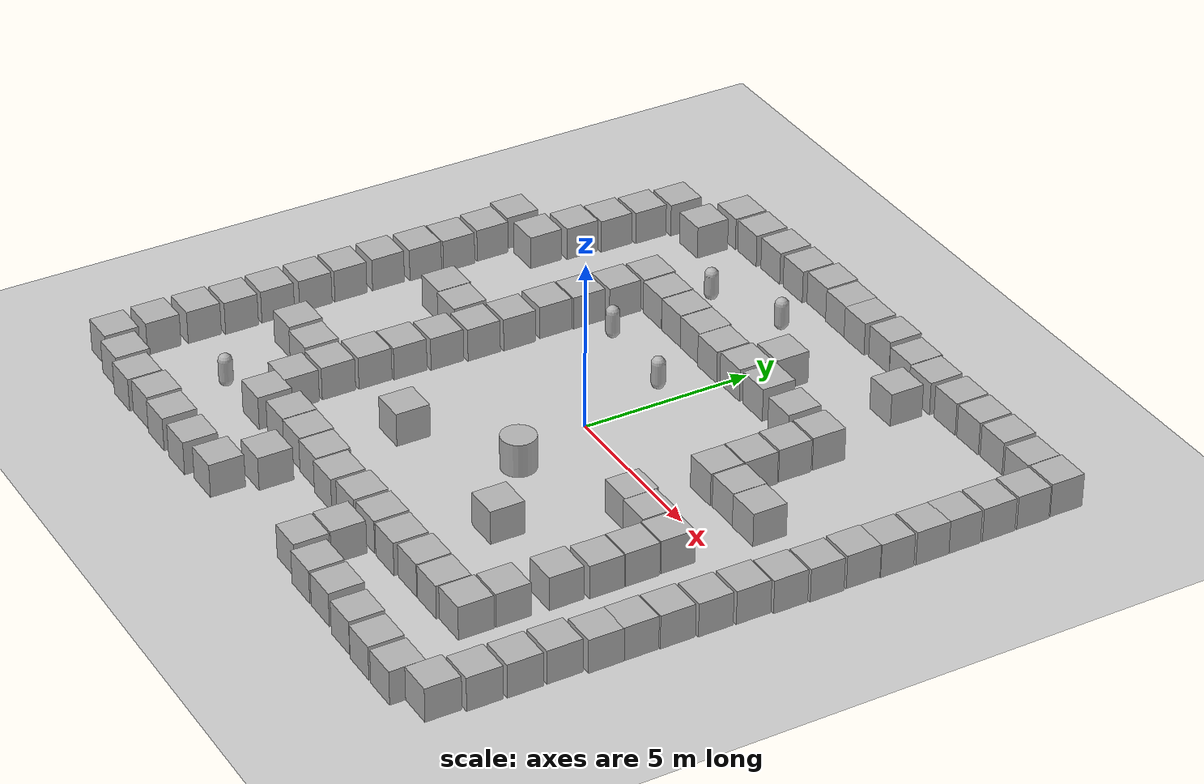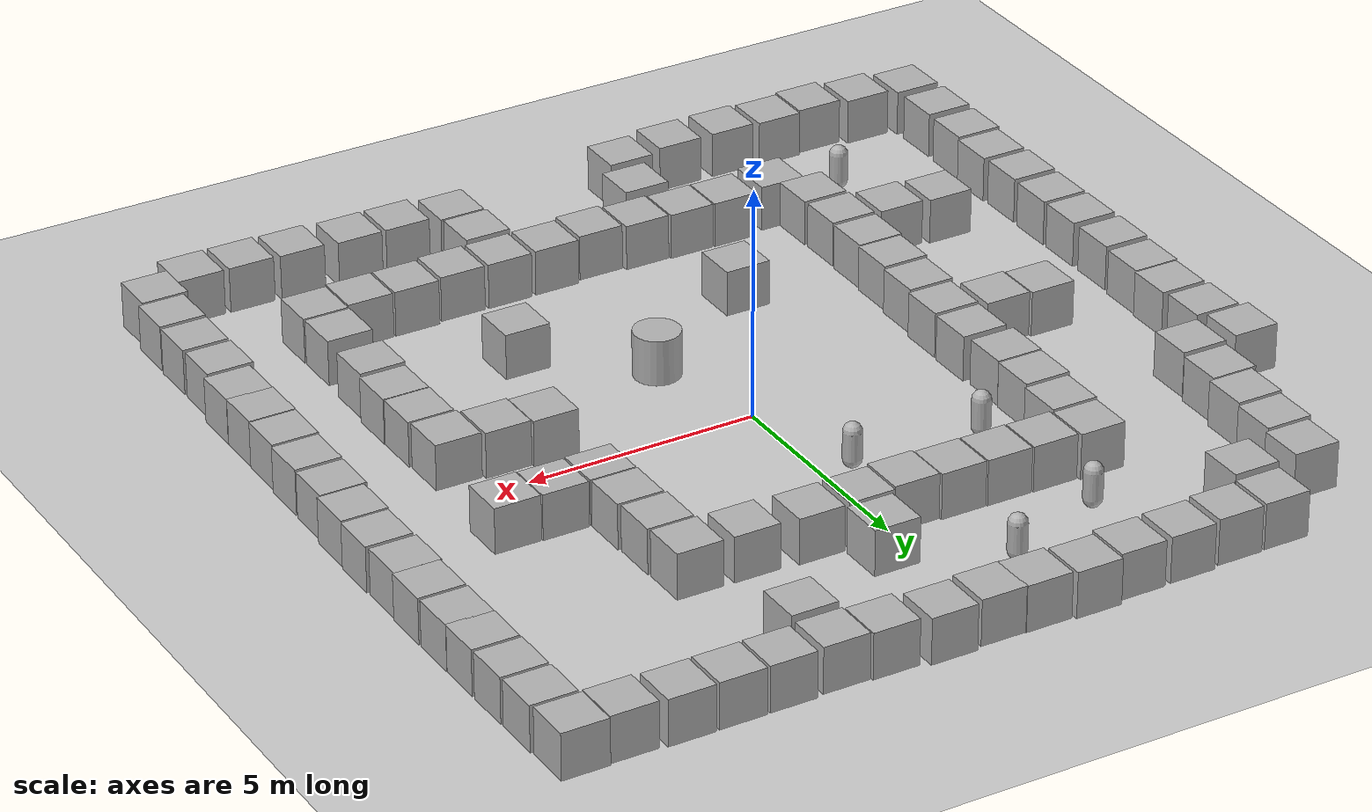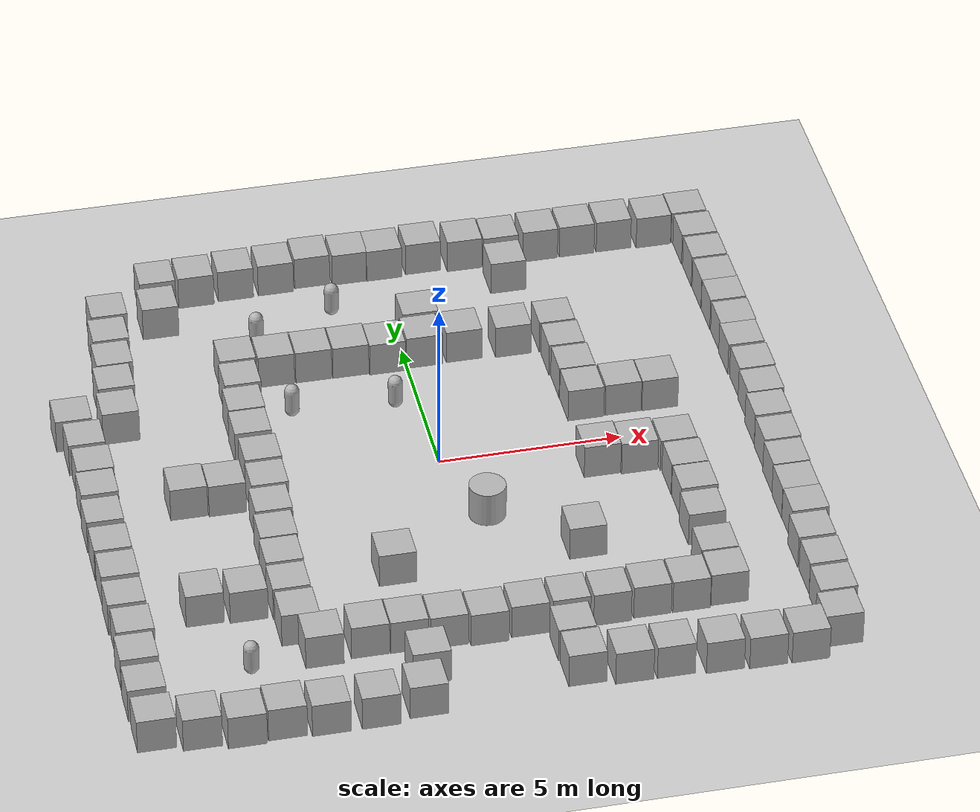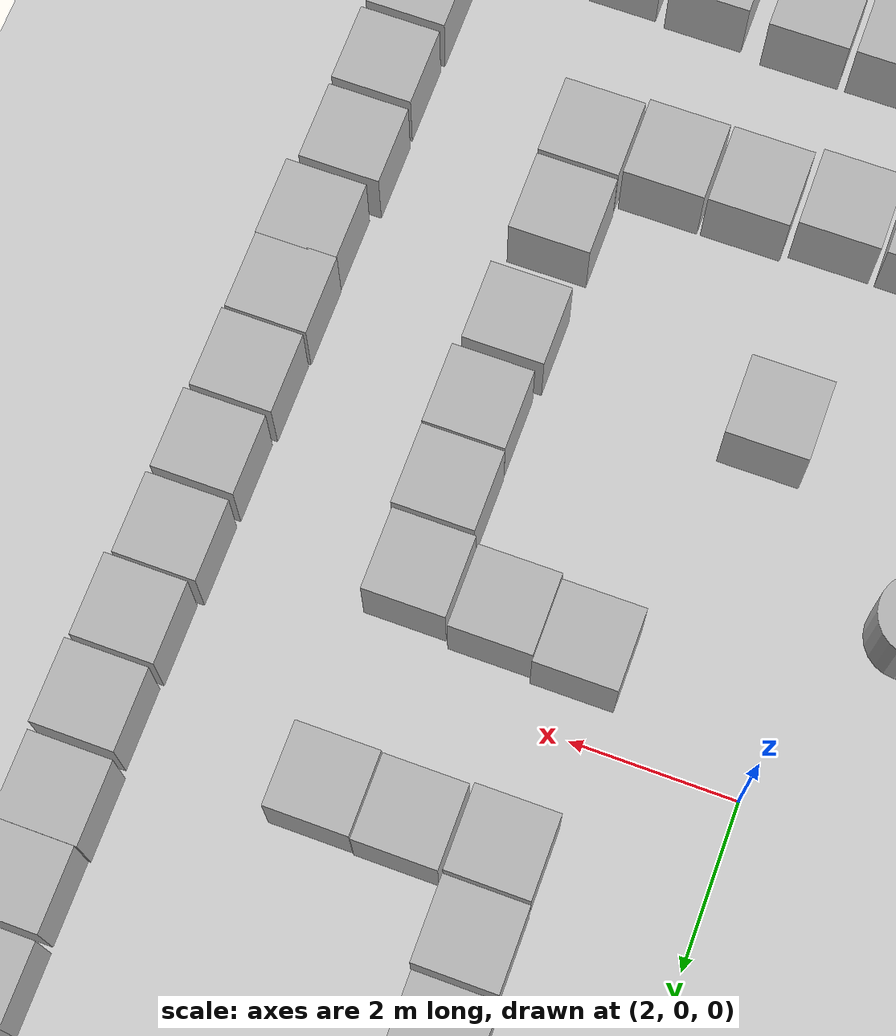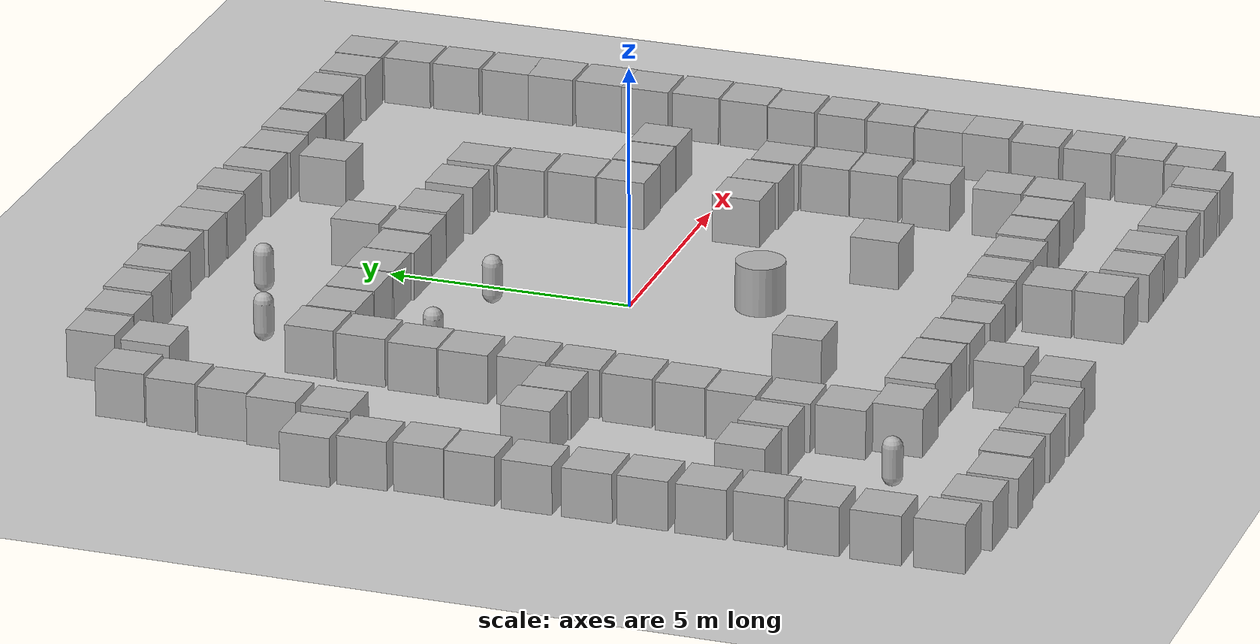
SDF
<sdf version='1.9'>
  <world name='empty'>
    <physics name='1ms' type='ignored'>
      <max_step_size>0.001</max_step_size>
      <real_time_factor>1</real_time_factor>
      <real_time_update_rate>1000</real_time_update_rate>
    </physics>
    <plugin name='gz::sim::systems::Physics' filename='ignition-gazebo-physics-system'/>
    <plugin name='gz::sim::systems::UserCommands' filename='ignition-gazebo-user-commands-system'/>
    <plugin name='gz::sim::systems::SceneBroadcaster' filename='ignition-gazebo-scene-broadcaster-system'/>
    <plugin name='gz::sim::systems::Contact' filename='ignition-gazebo-contact-system'/>
    <gravity>0 0 -9.8</gravity>
    <magnetic_field>6e-06 2.3e-05 -4.2e-05</magnetic_field>
    <atmosphere type='adiabatic'/>
    <scene>
      <ambient>0.4 0.4 0.4 1</ambient>
      <background>0.7 0.7 0.7 1</background>
      <shadows>true</shadows>
    </scene>
    <model name='ground_plane'>
      <static>true</static>
      <link name='link'>
        <collision name='collision'>
          <geometry>
            <plane>
              <normal>0 0 1</normal>
              <size>100 100</size>
            </plane>
          </geometry>
          <surface>
            <friction>
              <ode/>
            </friction>
            <bounce/>
            <contact/>
          </surface>
        </collision>
        <visual name='visual'>
          <geometry>
            <plane>
              <normal>0 0 1</normal>
              <size>100 100</size>
            </plane>
          </geometry>
          <material>
            <ambient>0.8 0.8 0.8 1</ambient>
            <diffuse>0.8 0.8 0.8 1</diffuse>
            <specular>0.8 0.8 0.8 1</specular>
          </material>
        </visual>
        <pose>0 0 0 0 -0 0</pose>
        <inertial>
          <pose>0 0 0 0 -0 0</pose>
          <mass>1</mass>
          <inertia>
            <ixx>1</ixx>
            <ixy>0</ixy>
            <ixz>0</ixz>
            <iyy>1</iyy>
            <iyz>0</iyz>
            <izz>1</izz>
          </inertia>
        </inertial>
        <enable_wind>false</enable_wind>
      </link>
      <pose>0 0 0 0 -0 0</pose>
      <self_collide>false</self_collide>
    </model>
    <model name='box'>
      <pose>4.25716 2.52176 0.5 0 -0 0</pose>
      <link name='box_link'>
        <inertial>
          <inertia>
            <ixx>0.16666</ixx>
            <ixy>0</ixy>
            <ixz>0</ixz>
            <iyy>0.16666</iyy>
            <iyz>0</iyz>
            <izz>0.16666</izz>
          </inertia>
          <mass>1</mass>
          <pose>0 0 0 0 -0 0</pose>
        </inertial>
        <collision name='box_collision'>
          <geometry>
            <box>
              <size>1 1 1</size>
            </box>
          </geometry>
          <surface>
            <friction>
              <ode/>
            </friction>
            <bounce/>
            <contact/>
          </surface>
        </collision>
        <visual name='box_visual'>
          <geometry>
            <box>
              <size>1 1 1</size>
            </box>
          </geometry>
          <material>
            <ambient>0.3 0.3 0.3 1</ambient>
            <diffuse>0.7 0.7 0.7 1</diffuse>
            <specular>1 1 1 1</specular>
          </material>
        </visual>
        <pose>0 0 0 0 -0 0</pose>
        <enable_wind>false</enable_wind>
      </link>
      <static>false</static>
      <self_collide>false</self_collide>
    </model>
    <model name='box_0'>
      <pose>4.26721 1.48635 0.5 0 -0 0</pose>
      <link name='box_link'>
        <inertial>
          <inertia>
            <ixx>0.16666</ixx>
            <ixy>0</ixy>
            <ixz>0</ixz>
            <iyy>0.16666</iyy>
            <iyz>0</iyz>
            <izz>0.16666</izz>
          </inertia>
          <mass>1</mass>
          <pose>0 0 0 0 -0 0</pose>
        </inertial>
        <collision name='box_collision'>
          <geometry>
            <box>
              <size>1 1 1</size>
            </box>
          </geometry>
          <surface>
            <friction>
              <ode/>
            </friction>
            <bounce/>
            <contact/>
          </surface>
        </collision>
        <visual name='box_visual'>
          <geometry>
            <box>
              <size>1 1 1</size>
            </box>
          </geometry>
          <material>
            <ambient>0.3 0.3 0.3 1</ambient>
            <diffuse>0.7 0.7 0.7 1</diffuse>
            <specular>1 1 1 1</specular>
          </material>
        </visual>
        <pose>0 0 0 0 -0 0</pose>
        <enable_wind>false</enable_wind>
      </link>
      <static>false</static>
      <self_collide>false</self_collide>
    </model>
    <model name='box_1'>
      <pose>5.31038 1.51759 0.5 0 -0 0</pose>
      <link name='box_link'>
        <inertial>
          <inertia>
            <ixx>0.16666</ixx>
            <ixy>0</ixy>
            <ixz>0</ixz>
            <iyy>0.16666</iyy>
            <iyz>0</iyz>
            <izz>0.16666</izz>
          </inertia>
          <mass>1</mass>
          <pose>0 0 0 0 -0 0</pose>
        </inertial>
        <collision name='box_collision'>
          <geometry>
            <box>
              <size>1 1 1</size>
            </box>
          </geometry>
          <surface>
            <friction>
              <ode/>
            </friction>
            <bounce/>
            <contact/>
          </surface>
        </collision>
        <visual name='box_visual'>
          <geometry>
            <box>
              <size>1 1 1</size>
            </box>
          </geometry>
          <material>
            <ambient>0.3 0.3 0.3 1</ambient>
            <diffuse>0.7 0.7 0.7 1</diffuse>
            <specular>1 1 1 1</specular>
          </material>
        </visual>
        <pose>0 0 0 0 -0 0</pose>
        <enable_wind>false</enable_wind>
      </link>
      <static>false</static>
      <self_collide>false</self_collide>
    </model>
    <model name='box_2'>
      <pose>4.13558 -0.985724 0.5 0 -0 0</pose>
      <link name='box_link'>
        <inertial>
          <inertia>
            <ixx>0.16666</ixx>
            <ixy>0</ixy>
            <ixz>0</ixz>
            <iyy>0.16666</iyy>
            <iyz>0</iyz>
            <izz>0.16666</izz>
          </inertia>
          <mass>1</mass>
          <pose>0 0 0 0 -0 0</pose>
        </inertial>
        <collision name='box_collision'>
          <geometry>
            <box>
              <size>1 1 1</size>
            </box>
          </geometry>
          <surface>
            <friction>
              <ode/>
            </friction>
            <bounce/>
            <contact/>
          </surface>
        </collision>
        <visual name='box_visual'>
          <geometry>
            <box>
              <size>1 1 1</size>
            </box>
          </geometry>
          <material>
            <ambient>0.3 0.3 0.3 1</ambient>
            <diffuse>0.7 0.7 0.7 1</diffuse>
            <specular>1 1 1 1</specular>
          </material>
        </visual>
        <pose>0 0 0 0 -0 0</pose>
        <enable_wind>false</enable_wind>
      </link>
      <static>false</static>
      <self_collide>false</self_collide>
    </model>
    <model name='box_3'>
      <pose>5.14532 -1.0495 0.5 0 -0 0</pose>
      <link name='box_link'>
        <inertial>
          <inertia>
            <ixx>0.16666</ixx>
            <ixy>0</ixy>
            <ixz>0</ixz>
            <iyy>0.16666</iyy>
            <iyz>0</iyz>
            <izz>0.16666</izz>
          </inertia>
          <mass>1</mass>
          <pose>0 0 0 0 -0 0</pose>
        </inertial>
        <collision name='box_collision'>
          <geometry>
            <box>
              <size>1 1 1</size>
            </box>
          </geometry>
          <surface>
            <friction>
              <ode/>
            </friction>
            <bounce/>
            <contact/>
          </surface>
        </collision>
        <visual name='box_visual'>
          <geometry>
            <box>
              <size>1 1 1</size>
            </box>
          </geometry>
          <material>
            <ambient>0.3 0.3 0.3 1</ambient>
            <diffuse>0.7 0.7 0.7 1</diffuse>
            <specular>1 1 1 1</specular>
          </material>
        </visual>
        <pose>0 0 0 0 -0 0</pose>
        <enable_wind>false</enable_wind>
      </link>
      <static>false</static>
      <self_collide>false</self_collide>
    </model>
    <model name='box_4'>
      <pose>6.19145 -1.12646 0.5 0 -0 0</pose>
      <link name='box_link'>
        <inertial>
          <inertia>
            <ixx>0.16666</ixx>
            <ixy>0</ixy>
            <ixz>0</ixz>
            <iyy>0.16666</iyy>
            <iyz>0</iyz>
            <izz>0.16666</izz>
          </inertia>
          <mass>1</mass>
          <pose>0 0 0 0 -0 0</pose>
        </inertial>
        <collision name='box_collision'>
          <geometry>
            <box>
              <size>1 1 1</size>
            </box>
          </geometry>
          <surface>
            <friction>
              <ode/>
            </friction>
            <bounce/>
            <contact/>
          </surface>
        </collision>
        <visual name='box_visual'>
          <geometry>
            <box>
              <size>1 1 1</size>
            </box>
          </geometry>
          <material>
            <ambient>0.3 0.3 0.3 1</ambient>
            <diffuse>0.7 0.7 0.7 1</diffuse>
            <specular>1 1 1 1</specular>
          </material>
        </visual>
        <pose>0 0 0 0 -0 0</pose>
        <enable_wind>false</enable_wind>
      </link>
      <static>false</static>
      <self_collide>false</self_collide>
    </model>
    <model name='box_5'>
      <pose>8.86919 -2.71605 0.5 0 -0 0</pose>
      <link name='box_link'>
        <inertial>
          <inertia>
            <ixx>0.16666</ixx>
            <ixy>0</ixy>
            <ixz>0</ixz>
            <iyy>0.16666</iyy>
            <iyz>0</iyz>
            <izz>0.16666</izz>
          </inertia>
          <mass>1</mass>
          <pose>0 0 0 0 -0 0</pose>
        </inertial>
        <collision name='box_collision'>
          <geometry>
            <box>
              <size>1 1 1</size>
            </box>
          </geometry>
          <surface>
            <friction>
              <ode/>
            </friction>
            <bounce/>
            <contact/>
          </surface>
        </collision>
        <visual name='box_visual'>
          <geometry>
            <box>
              <size>1 1 1</size>
            </box>
          </geometry>
          <material>
            <ambient>0.3 0.3 0.3 1</ambient>
            <diffuse>0.7 0.7 0.7 1</diffuse>
            <specular>1 1 1 1</specular>
          </material>
        </visual>
        <pose>0 0 0 0 -0 0</pose>
        <enable_wind>false</enable_wind>
      </link>
      <static>false</static>
      <self_collide>false</self_collide>
    </model>
    <model name='box_6'>
      <pose>6.22858 -2.1758 0.5 0 -0 0</pose>
      <link name='box_link'>
        <inertial>
          <inertia>
            <ixx>0.16666</ixx>
            <ixy>0</ixy>
            <ixz>0</ixz>
            <iyy>0.16666</iyy>
            <iyz>0</iyz>
            <izz>0.16666</izz>
          </inertia>
          <mass>1</mass>
          <pose>0 0 0 0 -0 0</pose>
        </inertial>
        <collision name='box_collision'>
          <geometry>
            <box>
              <size>1 1 1</size>
            </box>
          </geometry>
          <surface>
            <friction>
              <ode/>
            </friction>
            <bounce/>
            <contact/>
          </surface>
        </collision>
        <visual name='box_visual'>
          <geometry>
            <box>
              <size>1 1 1</size>
            </box>
          </geometry>
          <material>
            <ambient>0.3 0.3 0.3 1</ambient>
            <diffuse>0.7 0.7 0.7 1</diffuse>
            <specular>1 1 1 1</specular>
          </material>
        </visual>
        <pose>0 0 0 0 -0 0</pose>
        <enable_wind>false</enable_wind>
      </link>
      <static>false</static>
      <self_collide>false</self_collide>
    </model>
    <model name='box_7'>
      <pose>6.23565 -3.20198 0.5 0 -0 0</pose>
      <link name='box_link'>
        <inertial>
          <inertia>
            <ixx>0.16666</ixx>
            <ixy>0</ixy>
            <ixz>0</ixz>
            <iyy>0.16666</iyy>
            <iyz>0</iyz>
            <izz>0.16666</izz>
          </inertia>
          <mass>1</mass>
          <pose>0 0 0 0 -0 0</pose>
        </inertial>
        <collision name='box_collision'>
          <geometry>
            <box>
              <size>1 1 1</size>
            </box>
          </geometry>
          <surface>
            <friction>
              <ode/>
            </friction>
            <bounce/>
            <contact/>
          </surface>
        </collision>
        <visual name='box_visual'>
          <geometry>
            <box>
              <size>1 1 1</size>
            </box>
          </geometry>
          <material>
            <ambient>0.3 0.3 0.3 1</ambient>
            <diffuse>0.7 0.7 0.7 1</diffuse>
            <specular>1 1 1 1</specular>
          </material>
        </visual>
        <pose>0 0 0 0 -0 0</pose>
        <enable_wind>false</enable_wind>
      </link>
      <static>false</static>
      <self_collide>false</self_collide>
    </model>
    <model name='box_8'>
      <pose>6.1657 -4.3144 0.5 0 -0 0</pose>
      <link name='box_link'>
        <inertial>
          <inertia>
            <ixx>0.16666</ixx>
            <ixy>0</ixy>
            <ixz>0</ixz>
            <iyy>0.16666</iyy>
            <iyz>0</iyz>
            <izz>0.16666</izz>
          </inertia>
          <mass>1</mass>
          <pose>0 0 0 0 -0 0</pose>
        </inertial>
        <collision name='box_collision'>
          <geometry>
            <box>
              <size>1 1 1</size>
            </box>
          </geometry>
          <surface>
            <friction>
              <ode/>
            </friction>
            <bounce/>
            <contact/>
          </surface>
        </collision>
        <visual name='box_visual'>
          <geometry>
            <box>
              <size>1 1 1</size>
            </box>
          </geometry>
          <material>
            <ambient>0.3 0.3 0.3 1</ambient>
            <diffuse>0.7 0.7 0.7 1</diffuse>
            <specular>1 1 1 1</specular>
          </material>
        </visual>
        <pose>0 0 0 0 -0 0</pose>
        <enable_wind>false</enable_wind>
      </link>
      <static>false</static>
      <self_collide>false</self_collide>
    </model>
    <model name='box_9'>
      <pose>4.21655 3.58199 0.5 0 -0 0</pose>
      <link name='box_link'>
        <inertial>
          <inertia>
            <ixx>0.16666</ixx>
            <ixy>0</ixy>
            <ixz>0</ixz>
            <iyy>0.16666</iyy>
            <iyz>0</iyz>
            <izz>0.16666</izz>
          </inertia>
          <mass>1</mass>
          <pose>0 0 0 0 -0 0</pose>
        </inertial>
        <collision name='box_collision'>
          <geometry>
            <box>
              <size>1 1 1</size>
            </box>
          </geometry>
          <surface>
            <friction>
              <ode/>
            </friction>
            <bounce/>
            <contact/>
          </surface>
        </collision>
        <visual name='box_visual'>
          <geometry>
            <box>
              <size>1 1 1</size>
            </box>
          </geometry>
          <material>
            <ambient>0.3 0.3 0.3 1</ambient>
            <diffuse>0.7 0.7 0.7 1</diffuse>
            <specular>1 1 1 1</specular>
          </material>
        </visual>
        <pose>0 0 0 0 -0 0</pose>
        <enable_wind>false</enable_wind>
      </link>
      <static>false</static>
      <self_collide>false</self_collide>
    </model>
    <model name='box_10'>
      <pose>4.18778 4.6375 0.5 0 -0 0</pose>
      <link name='box_link'>
        <inertial>
          <inertia>
            <ixx>0.16666</ixx>
            <ixy>0</ixy>
            <ixz>0</ixz>
            <iyy>0.16666</iyy>
            <iyz>0</iyz>
            <izz>0.16666</izz>
          </inertia>
          <mass>1</mass>
          <pose>0 0 0 0 -0 0</pose>
        </inertial>
        <collision name='box_collision'>
          <geometry>
            <box>
              <size>1 1 1</size>
            </box>
          </geometry>
          <surface>
            <friction>
              <ode/>
            </friction>
            <bounce/>
            <contact/>
          </surface>
        </collision>
        <visual name='box_visual'>
          <geometry>
            <box>
              <size>1 1 1</size>
            </box>
          </geometry>
          <material>
            <ambient>0.3 0.3 0.3 1</ambient>
            <diffuse>0.7 0.7 0.7 1</diffuse>
            <specular>1 1 1 1</specular>
          </material>
        </visual>
        <pose>0 0 0 0 -0 0</pose>
        <enable_wind>false</enable_wind>
      </link>
      <static>false</static>
      <self_collide>false</self_collide>
    </model>
    <model name='box_11'>
      <pose>2.96363 4.6518 0.5 0 -0 0</pose>
      <link name='box_link'>
        <inertial>
          <inertia>
            <ixx>0.16666</ixx>
            <ixy>0</ixy>
            <ixz>0</ixz>
            <iyy>0.16666</iyy>
            <iyz>0</iyz>
            <izz>0.16666</izz>
          </inertia>
          <mass>1</mass>
          <pose>0 0 0 0 -0 0</pose>
        </inertial>
        <collision name='box_collision'>
          <geometry>
            <box>
              <size>1 1 1</size>
            </box>
          </geometry>
          <surface>
            <friction>
              <ode/>
            </friction>
            <bounce/>
            <contact/>
          </surface>
        </collision>
        <visual name='box_visual'>
          <geometry>
            <box>
              <size>1 1 1</size>
            </box>
          </geometry>
          <material>
            <ambient>0.3 0.3 0.3 1</ambient>
            <diffuse>0.7 0.7 0.7 1</diffuse>
            <specular>1 1 1 1</specular>
          </material>
        </visual>
        <pose>0 0 0 0 -0 0</pose>
        <enable_wind>false</enable_wind>
      </link>
      <static>false</static>
      <self_collide>false</self_collide>
    </model>
    <model name='box_12'>
      <pose>1.59067 4.71205 0.5 0 -0 0</pose>
      <link name='box_link'>
        <inertial>
          <inertia>
            <ixx>0.16666</ixx>
            <ixy>0</ixy>
            <ixz>0</ixz>
            <iyy>0.16666</iyy>
            <iyz>0</iyz>
            <izz>0.16666</izz>
          </inertia>
          <mass>1</mass>
          <pose>0 0 0 0 -0 0</pose>
        </inertial>
        <collision name='box_collision'>
          <geometry>
            <box>
              <size>1 1 1</size>
            </box>
          </geometry>
          <surface>
            <friction>
              <ode/>
            </friction>
            <bounce/>
            <contact/>
          </surface>
        </collision>
        <visual name='box_visual'>
          <geometry>
            <box>
              <size>1 1 1</size>
            </box>
          </geometry>
          <material>
            <ambient>0.3 0.3 0.3 1</ambient>
            <diffuse>0.7 0.7 0.7 1</diffuse>
            <specular>1 1 1 1</specular>
          </material>
        </visual>
        <pose>0 0 0 0 -0 0</pose>
        <enable_wind>false</enable_wind>
      </link>
      <static>false</static>
      <self_collide>false</self_collide>
    </model>
    <model name='box_13'>
      <pose>0.474826 4.68056 0.5 0 -0 0</pose>
      <link name='box_link'>
        <inertial>
          <inertia>
            <ixx>0.16666</ixx>
            <ixy>0</ixy>
            <ixz>0</ixz>
            <iyy>0.16666</iyy>
            <iyz>0</iyz>
            <izz>0.16666</izz>
          </inertia>
          <mass>1</mass>
          <pose>0 0 0 0 -0 0</pose>
        </inertial>
        <collision name='box_collision'>
          <geometry>
            <box>
              <size>1 1 1</size>
            </box>
          </geometry>
          <surface>
            <friction>
              <ode/>
            </friction>
            <bounce/>
            <contact/>
          </surface>
        </collision>
        <visual name='box_visual'>
          <geometry>
            <box>
              <size>1 1 1</size>
            </box>
          </geometry>
          <material>
            <ambient>0.3 0.3 0.3 1</ambient>
            <diffuse>0.7 0.7 0.7 1</diffuse>
            <specular>1 1 1 1</specular>
          </material>
        </visual>
        <pose>0 0 0 0 -0 0</pose>
        <enable_wind>false</enable_wind>
      </link>
      <static>false</static>
      <self_collide>false</self_collide>
    </model>
    <model name='box_14'>
      <pose>-0.571616 4.60503 0.5 0 -0 0</pose>
      <link name='box_link'>
        <inertial>
          <inertia>
            <ixx>0.16666</ixx>
            <ixy>0</ixy>
            <ixz>0</ixz>
            <iyy>0.16666</iyy>
            <iyz>0</iyz>
            <izz>0.16666</izz>
          </inertia>
          <mass>1</mass>
          <pose>0 0 0 0 -0 0</pose>
        </inertial>
        <collision name='box_collision'>
          <geometry>
            <box>
              <size>1 1 1</size>
            </box>
          </geometry>
          <surface>
            <friction>
              <ode/>
            </friction>
            <bounce/>
            <contact/>
          </surface>
        </collision>
        <visual name='box_visual'>
          <geometry>
            <box>
              <size>1 1 1</size>
            </box>
          </geometry>
          <material>
            <ambient>0.3 0.3 0.3 1</ambient>
            <diffuse>0.7 0.7 0.7 1</diffuse>
            <specular>1 1 1 1</specular>
          </material>
        </visual>
        <pose>0 0 0 0 -0 0</pose>
        <enable_wind>false</enable_wind>
      </link>
      <static>false</static>
      <self_collide>false</self_collide>
    </model>
    <model name='box_15'>
      <pose>-1.58468 4.66608 0.5 0 -0 0</pose>
      <link name='box_link'>
        <inertial>
          <inertia>
            <ixx>0.16666</ixx>
            <ixy>0</ixy>
            <ixz>0</ixz>
            <iyy>0.16666</iyy>
            <iyz>0</iyz>
            <izz>0.16666</izz>
          </inertia>
          <mass>1</mass>
          <pose>0 0 0 0 -0 0</pose>
        </inertial>
        <collision name='box_collision'>
          <geometry>
            <box>
              <size>1 1 1</size>
            </box>
          </geometry>
          <surface>
            <friction>
              <ode/>
            </friction>
            <bounce/>
            <contact/>
          </surface>
        </collision>
        <visual name='box_visual'>
          <geometry>
            <box>
              <size>1 1 1</size>
            </box>
          </geometry>
          <material>
            <ambient>0.3 0.3 0.3 1</ambient>
            <diffuse>0.7 0.7 0.7 1</diffuse>
            <specular>1 1 1 1</specular>
          </material>
        </visual>
        <pose>0 0 0 0 -0 0</pose>
        <enable_wind>false</enable_wind>
      </link>
      <static>false</static>
      <self_collide>false</self_collide>
    </model>
    <model name='box_16'>
      <pose>-2.61521 4.67735 0.5 0 -0 0</pose>
      <link name='box_link'>
        <inertial>
          <inertia>
            <ixx>0.16666</ixx>
            <ixy>0</ixy>
            <ixz>0</ixz>
            <iyy>0.16666</iyy>
            <iyz>0</iyz>
            <izz>0.16666</izz>
          </inertia>
          <mass>1</mass>
          <pose>0 0 0 0 -0 0</pose>
        </inertial>
        <collision name='box_collision'>
          <geometry>
            <box>
              <size>1 1 1</size>
            </box>
          </geometry>
          <surface>
            <friction>
              <ode/>
            </friction>
            <bounce/>
            <contact/>
          </surface>
        </collision>
        <visual name='box_visual'>
          <geometry>
            <box>
              <size>1 1 1</size>
            </box>
          </geometry>
          <material>
            <ambient>0.3 0.3 0.3 1</ambient>
            <diffuse>0.7 0.7 0.7 1</diffuse>
            <specular>1 1 1 1</specular>
          </material>
        </visual>
        <pose>0 0 0 0 -0 0</pose>
        <enable_wind>false</enable_wind>
      </link>
      <static>false</static>
      <self_collide>false</self_collide>
    </model>
    <model name='box_17'>
      <pose>-3.64818 4.6887 0.5 0 -0 0</pose>
      <link name='box_link'>
        <inertial>
          <inertia>
            <ixx>0.16666</ixx>
            <ixy>0</ixy>
            <ixz>0</ixz>
            <iyy>0.16666</iyy>
            <iyz>0</iyz>
            <izz>0.16666</izz>
          </inertia>
          <mass>1</mass>
          <pose>0 0 0 0 -0 0</pose>
        </inertial>
        <collision name='box_collision'>
          <geometry>
            <box>
              <size>1 1 1</size>
            </box>
          </geometry>
          <surface>
            <friction>
              <ode/>
            </friction>
            <bounce/>
            <contact/>
          </surface>
        </collision>
        <visual name='box_visual'>
          <geometry>
            <box>
              <size>1 1 1</size>
            </box>
          </geometry>
          <material>
            <ambient>0.3 0.3 0.3 1</ambient>
            <diffuse>0.7 0.7 0.7 1</diffuse>
            <specular>1 1 1 1</specular>
          </material>
        </visual>
        <pose>0 0 0 0 -0 0</pose>
        <enable_wind>false</enable_wind>
      </link>
      <static>false</static>
      <self_collide>false</self_collide>
    </model>
    <model name='box_18'>
      <pose>-4.69033 4.75286 0.5 0 -0 0</pose>
      <link name='box_link'>
        <inertial>
          <inertia>
            <ixx>0.16666</ixx>
            <ixy>0</ixy>
            <ixz>0</ixz>
            <iyy>0.16666</iyy>
            <iyz>0</iyz>
            <izz>0.16666</izz>
          </inertia>
          <mass>1</mass>
          <pose>0 0 0 0 -0 0</pose>
        </inertial>
        <collision name='box_collision'>
          <geometry>
            <box>
              <size>1 1 1</size>
            </box>
          </geometry>
          <surface>
            <friction>
              <ode/>
            </friction>
            <bounce/>
            <contact/>
          </surface>
        </collision>
        <visual name='box_visual'>
          <geometry>
            <box>
              <size>1 1 1</size>
            </box>
          </geometry>
          <material>
            <ambient>0.3 0.3 0.3 1</ambient>
            <diffuse>0.7 0.7 0.7 1</diffuse>
            <specular>1 1 1 1</specular>
          </material>
        </visual>
        <pose>0 0 0 0 -0 0</pose>
        <enable_wind>false</enable_wind>
      </link>
      <static>false</static>
      <self_collide>false</self_collide>
    </model>
    <model name='box_19'>
      <pose>-4.74822 3.67565 0.5 0 -0 0</pose>
      <link name='box_link'>
        <inertial>
          <inertia>
            <ixx>0.16666</ixx>
            <ixy>0</ixy>
            <ixz>0</ixz>
            <iyy>0.16666</iyy>
            <iyz>0</iyz>
            <izz>0.16666</izz>
          </inertia>
          <mass>1</mass>
          <pose>0 0 0 0 -0 0</pose>
        </inertial>
        <collision name='box_collision'>
          <geometry>
            <box>
              <size>1 1 1</size>
            </box>
          </geometry>
          <surface>
            <friction>
              <ode/>
            </friction>
            <bounce/>
            <contact/>
          </surface>
        </collision>
        <visual name='box_visual'>
          <geometry>
            <box>
              <size>1 1 1</size>
            </box>
          </geometry>
          <material>
            <ambient>0.3 0.3 0.3 1</ambient>
            <diffuse>0.7 0.7 0.7 1</diffuse>
            <specular>1 1 1 1</specular>
          </material>
        </visual>
        <pose>0 0 0 0 -0 0</pose>
        <enable_wind>false</enable_wind>
      </link>
      <static>false</static>
      <self_collide>false</self_collide>
    </model>
    <model name='box_20'>
      <pose>-4.84161 2.58379 0.5 0 -0 0</pose>
      <link name='box_link'>
        <inertial>
          <inertia>
            <ixx>0.16666</ixx>
            <ixy>0</ixy>
            <ixz>0</ixz>
            <iyy>0.16666</iyy>
            <iyz>0</iyz>
            <izz>0.16666</izz>
          </inertia>
          <mass>1</mass>
          <pose>0 0 0 0 -0 0</pose>
        </inertial>
        <collision name='box_collision'>
          <geometry>
            <box>
              <size>1 1 1</size>
            </box>
          </geometry>
          <surface>
            <friction>
              <ode/>
            </friction>
            <bounce/>
            <contact/>
          </surface>
        </collision>
        <visual name='box_visual'>
          <geometry>
            <box>
              <size>1 1 1</size>
            </box>
          </geometry>
          <material>
            <ambient>0.3 0.3 0.3 1</ambient>
            <diffuse>0.7 0.7 0.7 1</diffuse>
            <specular>1 1 1 1</specular>
          </material>
        </visual>
        <pose>0 0 0 0 -0 0</pose>
        <enable_wind>false</enable_wind>
      </link>
      <static>false</static>
      <self_collide>false</self_collide>
    </model>
    <model name='box_21'>
      <pose>-4.86638 1.5426 0.5 0 -0 0</pose>
      <link name='box_link'>
        <inertial>
          <inertia>
            <ixx>0.16666</ixx>
            <ixy>0</ixy>
            <ixz>0</ixz>
            <iyy>0.16666</iyy>
            <iyz>0</iyz>
            <izz>0.16666</izz>
          </inertia>
          <mass>1</mass>
          <pose>0 0 0 0 -0 0</pose>
        </inertial>
        <collision name='box_collision'>
          <geometry>
            <box>
              <size>1 1 1</size>
            </box>
          </geometry>
          <surface>
            <friction>
              <ode/>
            </friction>
            <bounce/>
            <contact/>
          </surface>
        </collision>
        <visual name='box_visual'>
          <geometry>
            <box>
              <size>1 1 1</size>
            </box>
          </geometry>
          <material>
            <ambient>0.3 0.3 0.3 1</ambient>
            <diffuse>0.7 0.7 0.7 1</diffuse>
            <specular>1 1 1 1</specular>
          </material>
        </visual>
        <pose>0 0 0 0 -0 0</pose>
        <enable_wind>false</enable_wind>
      </link>
      <static>false</static>
      <self_collide>false</self_collide>
    </model>
    <model name='box_22'>
      <pose>-4.80389 0.380437 0.5 0 -0 0</pose>
      <link name='box_link'>
        <inertial>
          <inertia>
            <ixx>0.16666</ixx>
            <ixy>0</ixy>
            <ixz>0</ixz>
            <iyy>0.16666</iyy>
            <iyz>0</iyz>
            <izz>0.16666</izz>
          </inertia>
          <mass>1</mass>
          <pose>0 0 0 0 -0 0</pose>
        </inertial>
        <collision name='box_collision'>
          <geometry>
            <box>
              <size>1 1 1</size>
            </box>
          </geometry>
          <surface>
            <friction>
              <ode/>
            </friction>
            <bounce/>
            <contact/>
          </surface>
        </collision>
        <visual name='box_visual'>
          <geometry>
            <box>
              <size>1 1 1</size>
            </box>
          </geometry>
          <material>
            <ambient>0.3 0.3 0.3 1</ambient>
            <diffuse>0.7 0.7 0.7 1</diffuse>
            <specular>1 1 1 1</specular>
          </material>
        </visual>
        <pose>0 0 0 0 -0 0</pose>
        <enable_wind>false</enable_wind>
      </link>
      <static>false</static>
      <self_collide>false</self_collide>
    </model>
    <model name='box_23'>
      <pose>-4.83006 -0.710249 0.5 0 -0 0</pose>
      <link name='box_link'>
        <inertial>
          <inertia>
            <ixx>0.16666</ixx>
            <ixy>0</ixy>
            <ixz>0</ixz>
            <iyy>0.16666</iyy>
            <iyz>0</iyz>
            <izz>0.16666</izz>
          </inertia>
          <mass>1</mass>
          <pose>0 0 0 0 -0 0</pose>
        </inertial>
        <collision name='box_collision'>
          <geometry>
            <box>
              <size>1 1 1</size>
            </box>
          </geometry>
          <surface>
            <friction>
              <ode/>
            </friction>
            <bounce/>
            <contact/>
          </surface>
        </collision>
        <visual name='box_visual'>
          <geometry>
            <box>
              <size>1 1 1</size>
            </box>
          </geometry>
          <material>
            <ambient>0.3 0.3 0.3 1</ambient>
            <diffuse>0.7 0.7 0.7 1</diffuse>
            <specular>1 1 1 1</specular>
          </material>
        </visual>
        <pose>0 0 0 0 -0 0</pose>
        <enable_wind>false</enable_wind>
      </link>
      <static>false</static>
      <self_collide>false</self_collide>
    </model>
    <model name='box_24'>
      <pose>-4.92357 -1.79655 0.5 0 -0 0</pose>
      <link name='box_link'>
        <inertial>
          <inertia>
            <ixx>0.16666</ixx>
            <ixy>0</ixy>
            <ixz>0</ixz>
            <iyy>0.16666</iyy>
            <iyz>0</iyz>
            <izz>0.16666</izz>
          </inertia>
          <mass>1</mass>
          <pose>0 0 0 0 -0 0</pose>
        </inertial>
        <collision name='box_collision'>
          <geometry>
            <box>
              <size>1 1 1</size>
            </box>
          </geometry>
          <surface>
            <friction>
              <ode/>
            </friction>
            <bounce/>
            <contact/>
          </surface>
        </collision>
        <visual name='box_visual'>
          <geometry>
            <box>
              <size>1 1 1</size>
            </box>
          </geometry>
          <material>
            <ambient>0.3 0.3 0.3 1</ambient>
            <diffuse>0.7 0.7 0.7 1</diffuse>
            <specular>1 1 1 1</specular>
          </material>
        </visual>
        <pose>0 0 0 0 -0 0</pose>
        <enable_wind>false</enable_wind>
      </link>
      <static>false</static>
      <self_collide>false</self_collide>
    </model>
    <model name='box_25'>
      <pose>-4.99469 -2.88184 0.5 0 -0 0</pose>
      <link name='box_link'>
        <inertial>
          <inertia>
            <ixx>0.16666</ixx>
            <ixy>0</ixy>
            <ixz>0</ixz>
            <iyy>0.16666</iyy>
            <iyz>0</iyz>
            <izz>0.16666</izz>
          </inertia>
          <mass>1</mass>
          <pose>0 0 0 0 -0 0</pose>
        </inertial>
        <collision name='box_collision'>
          <geometry>
            <box>
              <size>1 1 1</size>
            </box>
          </geometry>
          <surface>
            <friction>
              <ode/>
            </friction>
            <bounce/>
            <contact/>
          </surface>
        </collision>
        <visual name='box_visual'>
          <geometry>
            <box>
              <size>1 1 1</size>
            </box>
          </geometry>
          <material>
            <ambient>0.3 0.3 0.3 1</ambient>
            <diffuse>0.7 0.7 0.7 1</diffuse>
            <specular>1 1 1 1</specular>
          </material>
        </visual>
        <pose>0 0 0 0 -0 0</pose>
        <enable_wind>false</enable_wind>
      </link>
      <static>false</static>
      <self_collide>false</self_collide>
    </model>
    <model name='box_26'>
      <pose>-5.04236 -3.92055 0.5 0 -0 0</pose>
      <link name='box_link'>
        <inertial>
          <inertia>
            <ixx>0.16666</ixx>
            <ixy>0</ixy>
            <ixz>0</ixz>
            <iyy>0.16666</iyy>
            <iyz>0</iyz>
            <izz>0.16666</izz>
          </inertia>
          <mass>1</mass>
          <pose>0 0 0 0 -0 0</pose>
        </inertial>
        <collision name='box_collision'>
          <geometry>
            <box>
              <size>1 1 1</size>
            </box>
          </geometry>
          <surface>
            <friction>
              <ode/>
            </friction>
            <bounce/>
            <contact/>
          </surface>
        </collision>
        <visual name='box_visual'>
          <geometry>
            <box>
              <size>1 1 1</size>
            </box>
          </geometry>
          <material>
            <ambient>0.3 0.3 0.3 1</ambient>
            <diffuse>0.7 0.7 0.7 1</diffuse>
            <specular>1 1 1 1</specular>
          </material>
        </visual>
        <pose>0 0 0 0 -0 0</pose>
        <enable_wind>false</enable_wind>
      </link>
      <static>false</static>
      <self_collide>false</self_collide>
    </model>
    <model name='box_27'>
      <pose>-5.06868 -5.00835 0.5 0 -0 0</pose>
      <link name='box_link'>
        <inertial>
          <inertia>
            <ixx>0.16666</ixx>
            <ixy>0</ixy>
            <ixz>0</ixz>
            <iyy>0.16666</iyy>
            <iyz>0</iyz>
            <izz>0.16666</izz>
          </inertia>
          <mass>1</mass>
          <pose>0 0 0 0 -0 0</pose>
        </inertial>
        <collision name='box_collision'>
          <geometry>
            <box>
              <size>1 1 1</size>
            </box>
          </geometry>
          <surface>
            <friction>
              <ode/>
            </friction>
            <bounce/>
            <contact/>
          </surface>
        </collision>
        <visual name='box_visual'>
          <geometry>
            <box>
              <size>1 1 1</size>
            </box>
          </geometry>
          <material>
            <ambient>0.3 0.3 0.3 1</ambient>
            <diffuse>0.7 0.7 0.7 1</diffuse>
            <specular>1 1 1 1</specular>
          </material>
        </visual>
        <pose>0 0 0 0 -0 0</pose>
        <enable_wind>false</enable_wind>
      </link>
      <static>false</static>
      <self_collide>false</self_collide>
    </model>
    <model name='box_28'>
      <pose>-5.0497 -6.10238 0.5 0 -0 0</pose>
      <link name='box_link'>
        <inertial>
          <inertia>
            <ixx>0.16666</ixx>
            <ixy>0</ixy>
            <ixz>0</ixz>
            <iyy>0.16666</iyy>
            <iyz>0</iyz>
            <izz>0.16666</izz>
          </inertia>
          <mass>1</mass>
          <pose>0 0 0 0 -0 0</pose>
        </inertial>
        <collision name='box_collision'>
          <geometry>
            <box>
              <size>1 1 1</size>
            </box>
          </geometry>
          <surface>
            <friction>
              <ode/>
            </friction>
            <bounce/>
            <contact/>
          </surface>
        </collision>
        <visual name='box_visual'>
          <geometry>
            <box>
              <size>1 1 1</size>
            </box>
          </geometry>
          <material>
            <ambient>0.3 0.3 0.3 1</ambient>
            <diffuse>0.7 0.7 0.7 1</diffuse>
            <specular>1 1 1 1</specular>
          </material>
        </visual>
        <pose>0 0 0 0 -0 0</pose>
        <enable_wind>false</enable_wind>
      </link>
      <static>false</static>
      <self_collide>false</self_collide>
    </model>
    <model name='box_29'>
      <pose>6.12407 -5.79524 0.5 0 -0 0</pose>
      <link name='box_link'>
        <inertial>
          <inertia>
            <ixx>0.16666</ixx>
            <ixy>0</ixy>
            <ixz>0</ixz>
            <iyy>0.16666</iyy>
            <iyz>0</iyz>
            <izz>0.16666</izz>
          </inertia>
          <mass>1</mass>
          <pose>0 0 0 0 -0 0</pose>
        </inertial>
        <collision name='box_collision'>
          <geometry>
            <box>
              <size>1 1 1</size>
            </box>
          </geometry>
          <surface>
            <friction>
              <ode/>
            </friction>
            <bounce/>
            <contact/>
          </surface>
        </collision>
        <visual name='box_visual'>
          <geometry>
            <box>
              <size>1 1 1</size>
            </box>
          </geometry>
          <material>
            <ambient>0.3 0.3 0.3 1</ambient>
            <diffuse>0.7 0.7 0.7 1</diffuse>
            <specular>1 1 1 1</specular>
          </material>
        </visual>
        <pose>0 0 0 0 -0 0</pose>
        <enable_wind>false</enable_wind>
      </link>
      <static>false</static>
      <self_collide>false</self_collide>
    </model>
    <model name='box_30'>
      <pose>6.13132 -6.8447 0.5 0 -0 0</pose>
      <link name='box_link'>
        <inertial>
          <inertia>
            <ixx>0.16666</ixx>
            <ixy>0</ixy>
            <ixz>0</ixz>
            <iyy>0.16666</iyy>
            <iyz>0</iyz>
            <izz>0.16666</izz>
          </inertia>
          <mass>1</mass>
          <pose>0 0 0 0 -0 0</pose>
        </inertial>
        <collision name='box_collision'>
          <geometry>
            <box>
              <size>1 1 1</size>
            </box>
          </geometry>
          <surface>
            <friction>
              <ode/>
            </friction>
            <bounce/>
            <contact/>
          </surface>
        </collision>
        <visual name='box_visual'>
          <geometry>
            <box>
              <size>1 1 1</size>
            </box>
          </geometry>
          <material>
            <ambient>0.3 0.3 0.3 1</ambient>
            <diffuse>0.7 0.7 0.7 1</diffuse>
            <specular>1 1 1 1</specular>
          </material>
        </visual>
        <pose>0 0 0 0 -0 0</pose>
        <enable_wind>false</enable_wind>
      </link>
      <static>false</static>
      <self_collide>false</self_collide>
    </model>
    <model name='box_31'>
      <pose>5.09836 -6.91237 0.5 0 -0 0</pose>
      <link name='box_link'>
        <inertial>
          <inertia>
            <ixx>0.16666</ixx>
            <ixy>0</ixy>
            <ixz>0</ixz>
            <iyy>0.16666</iyy>
            <iyz>0</iyz>
            <izz>0.16666</izz>
          </inertia>
          <mass>1</mass>
          <pose>0 0 0 0 -0 0</pose>
        </inertial>
        <collision name='box_collision'>
          <geometry>
            <box>
              <size>1 1 1</size>
            </box>
          </geometry>
          <surface>
            <friction>
              <ode/>
            </friction>
            <bounce/>
            <contact/>
          </surface>
        </collision>
        <visual name='box_visual'>
          <geometry>
            <box>
              <size>1 1 1</size>
            </box>
          </geometry>
          <material>
            <ambient>0.3 0.3 0.3 1</ambient>
            <diffuse>0.7 0.7 0.7 1</diffuse>
            <specular>1 1 1 1</specular>
          </material>
        </visual>
        <pose>0 0 0 0 -0 0</pose>
        <enable_wind>false</enable_wind>
      </link>
      <static>false</static>
      <self_collide>false</self_collide>
    </model>
    <model name='box_32'>
      <pose>4.05564 -6.91326 0.5 0 -0 0</pose>
      <link name='box_link'>
        <inertial>
          <inertia>
            <ixx>0.16666</ixx>
            <ixy>0</ixy>
            <ixz>0</ixz>
            <iyy>0.16666</iyy>
            <iyz>0</iyz>
            <izz>0.16666</izz>
          </inertia>
          <mass>1</mass>
          <pose>0 0 0 0 -0 0</pose>
        </inertial>
        <collision name='box_collision'>
          <geometry>
            <box>
              <size>1 1 1</size>
            </box>
          </geometry>
          <surface>
            <friction>
              <ode/>
            </friction>
            <bounce/>
            <contact/>
          </surface>
        </collision>
        <visual name='box_visual'>
          <geometry>
            <box>
              <size>1 1 1</size>
            </box>
          </geometry>
          <material>
            <ambient>0.3 0.3 0.3 1</ambient>
            <diffuse>0.7 0.7 0.7 1</diffuse>
            <specular>1 1 1 1</specular>
          </material>
        </visual>
        <pose>0 0 0 0 -0 0</pose>
        <enable_wind>false</enable_wind>
      </link>
      <static>false</static>
      <self_collide>false</self_collide>
    </model>
    <model name='box_33'>
      <pose>2.97347 -6.99341 0.5 0 -0 0</pose>
      <link name='box_link'>
        <inertial>
          <inertia>
            <ixx>0.16666</ixx>
            <ixy>0</ixy>
            <ixz>0</ixz>
            <iyy>0.16666</iyy>
            <iyz>0</iyz>
            <izz>0.16666</izz>
          </inertia>
          <mass>1</mass>
          <pose>0 0 0 0 -0 0</pose>
        </inertial>
        <collision name='box_collision'>
          <geometry>
            <box>
              <size>1 1 1</size>
            </box>
          </geometry>
          <surface>
            <friction>
              <ode/>
            </friction>
            <bounce/>
            <contact/>
          </surface>
        </collision>
        <visual name='box_visual'>
          <geometry>
            <box>
              <size>1 1 1</size>
            </box>
          </geometry>
          <material>
            <ambient>0.3 0.3 0.3 1</ambient>
            <diffuse>0.7 0.7 0.7 1</diffuse>
            <specular>1 1 1 1</specular>
          </material>
        </visual>
        <pose>0 0 0 0 -0 0</pose>
        <enable_wind>false</enable_wind>
      </link>
      <static>false</static>
      <self_collide>false</self_collide>
    </model>
    <model name='box_34'>
      <pose>1.89461 -6.98248 0.5 0 -0 0</pose>
      <link name='box_link'>
        <inertial>
          <inertia>
            <ixx>0.16666</ixx>
            <ixy>0</ixy>
            <ixz>0</ixz>
            <iyy>0.16666</iyy>
            <iyz>0</iyz>
            <izz>0.16666</izz>
          </inertia>
          <mass>1</mass>
          <pose>0 0 0 0 -0 0</pose>
        </inertial>
        <collision name='box_collision'>
          <geometry>
            <box>
              <size>1 1 1</size>
            </box>
          </geometry>
          <surface>
            <friction>
              <ode/>
            </friction>
            <bounce/>
            <contact/>
          </surface>
        </collision>
        <visual name='box_visual'>
          <geometry>
            <box>
              <size>1 1 1</size>
            </box>
          </geometry>
          <material>
            <ambient>0.3 0.3 0.3 1</ambient>
            <diffuse>0.7 0.7 0.7 1</diffuse>
            <specular>1 1 1 1</specular>
          </material>
        </visual>
        <pose>0 0 0 0 -0 0</pose>
        <enable_wind>false</enable_wind>
      </link>
      <static>false</static>
      <self_collide>false</self_collide>
    </model>
    <model name='box_35'>
      <pose>0.79959 -7.00351 0.5 0 -0 0</pose>
      <link name='box_link'>
        <inertial>
          <inertia>
            <ixx>0.16666</ixx>
            <ixy>0</ixy>
            <ixz>0</ixz>
            <iyy>0.16666</iyy>
            <iyz>0</iyz>
            <izz>0.16666</izz>
          </inertia>
          <mass>1</mass>
          <pose>0 0 0 0 -0 0</pose>
        </inertial>
        <collision name='box_collision'>
          <geometry>
            <box>
              <size>1 1 1</size>
            </box>
          </geometry>
          <surface>
            <friction>
              <ode/>
            </friction>
            <bounce/>
            <contact/>
          </surface>
        </collision>
        <visual name='box_visual'>
          <geometry>
            <box>
              <size>1 1 1</size>
            </box>
          </geometry>
          <material>
            <ambient>0.3 0.3 0.3 1</ambient>
            <diffuse>0.7 0.7 0.7 1</diffuse>
            <specular>1 1 1 1</specular>
          </material>
        </visual>
        <pose>0 0 0 0 -0 0</pose>
        <enable_wind>false</enable_wind>
      </link>
      <static>false</static>
      <self_collide>false</self_collide>
    </model>
    <model name='box_36'>
      <pose>-0.288194 -7.10821 0.5 0 -0 0</pose>
      <link name='box_link'>
        <inertial>
          <inertia>
            <ixx>0.16666</ixx>
            <ixy>0</ixy>
            <ixz>0</ixz>
            <iyy>0.16666</iyy>
            <iyz>0</iyz>
            <izz>0.16666</izz>
          </inertia>
          <mass>1</mass>
          <pose>0 0 0 0 -0 0</pose>
        </inertial>
        <collision name='box_collision'>
          <geometry>
            <box>
              <size>1 1 1</size>
            </box>
          </geometry>
          <surface>
            <friction>
              <ode/>
            </friction>
            <bounce/>
            <contact/>
          </surface>
        </collision>
        <visual name='box_visual'>
          <geometry>
            <box>
              <size>1 1 1</size>
            </box>
          </geometry>
          <material>
            <ambient>0.3 0.3 0.3 1</ambient>
            <diffuse>0.7 0.7 0.7 1</diffuse>
            <specular>1 1 1 1</specular>
          </material>
        </visual>
        <pose>0 0 0 0 -0 0</pose>
        <enable_wind>false</enable_wind>
      </link>
      <static>false</static>
      <self_collide>false</self_collide>
    </model>
    <model name='box_37'>
      <pose>-1.33272 -7.01143 0.5 0 -0 0</pose>
      <link name='box_link'>
        <inertial>
          <inertia>
            <ixx>0.16666</ixx>
            <ixy>0</ixy>
            <ixz>0</ixz>
            <iyy>0.16666</iyy>
            <iyz>0</iyz>
            <izz>0.16666</izz>
          </inertia>
          <mass>1</mass>
          <pose>0 0 0 0 -0 0</pose>
        </inertial>
        <collision name='box_collision'>
          <geometry>
            <box>
              <size>1 1 1</size>
            </box>
          </geometry>
          <surface>
            <friction>
              <ode/>
            </friction>
            <bounce/>
            <contact/>
          </surface>
        </collision>
        <visual name='box_visual'>
          <geometry>
            <box>
              <size>1 1 1</size>
            </box>
          </geometry>
          <material>
            <ambient>0.3 0.3 0.3 1</ambient>
            <diffuse>0.7 0.7 0.7 1</diffuse>
            <specular>1 1 1 1</specular>
          </material>
        </visual>
        <pose>0 0 0 0 -0 0</pose>
        <enable_wind>false</enable_wind>
      </link>
      <static>false</static>
      <self_collide>false</self_collide>
    </model>
    <model name='box_38'>
      <pose>-2.36921 -6.97202 0.5 0 -0 0</pose>
      <link name='box_link'>
        <inertial>
          <inertia>
            <ixx>0.16666</ixx>
            <ixy>0</ixy>
            <ixz>0</ixz>
            <iyy>0.16666</iyy>
            <iyz>0</iyz>
            <izz>0.16666</izz>
          </inertia>
          <mass>1</mass>
          <pose>0 0 0 0 -0 0</pose>
        </inertial>
        <collision name='box_collision'>
          <geometry>
            <box>
              <size>1 1 1</size>
            </box>
          </geometry>
          <surface>
            <friction>
              <ode/>
            </friction>
            <bounce/>
            <contact/>
          </surface>
        </collision>
        <visual name='box_visual'>
          <geometry>
            <box>
              <size>1 1 1</size>
            </box>
          </geometry>
          <material>
            <ambient>0.3 0.3 0.3 1</ambient>
            <diffuse>0.7 0.7 0.7 1</diffuse>
            <specular>1 1 1 1</specular>
          </material>
        </visual>
        <pose>0 0 0 0 -0 0</pose>
        <enable_wind>false</enable_wind>
      </link>
      <static>false</static>
      <self_collide>false</self_collide>
    </model>
    <model name='box_39'>
      <pose>-3.39624 -6.95954 0.5 0 -0 0</pose>
      <link name='box_link'>
        <inertial>
          <inertia>
            <ixx>0.16666</ixx>
            <ixy>0</ixy>
            <ixz>0</ixz>
            <iyy>0.16666</iyy>
            <iyz>0</iyz>
            <izz>0.16666</izz>
          </inertia>
          <mass>1</mass>
          <pose>0 0 0 0 -0 0</pose>
        </inertial>
        <collision name='box_collision'>
          <geometry>
            <box>
              <size>1 1 1</size>
            </box>
          </geometry>
          <surface>
            <friction>
              <ode/>
            </friction>
            <bounce/>
            <contact/>
          </surface>
        </collision>
        <visual name='box_visual'>
          <geometry>
            <box>
              <size>1 1 1</size>
            </box>
          </geometry>
          <material>
            <ambient>0.3 0.3 0.3 1</ambient>
            <diffuse>0.7 0.7 0.7 1</diffuse>
            <specular>1 1 1 1</specular>
          </material>
        </visual>
        <pose>0 0 0 0 -0 0</pose>
        <enable_wind>false</enable_wind>
      </link>
      <static>false</static>
      <self_collide>false</self_collide>
    </model>
    <model name='box_40'>
      <pose>-4.61406 -7.09221 0.5 0 -0 0</pose>
      <link name='box_link'>
        <inertial>
          <inertia>
            <ixx>0.16666</ixx>
            <ixy>0</ixy>
            <ixz>0</ixz>
            <iyy>0.16666</iyy>
            <iyz>0</iyz>
            <izz>0.16666</izz>
          </inertia>
          <mass>1</mass>
          <pose>0 0 0 0 -0 0</pose>
        </inertial>
        <collision name='box_collision'>
          <geometry>
            <box>
              <size>1 1 1</size>
            </box>
          </geometry>
          <surface>
            <friction>
              <ode/>
            </friction>
            <bounce/>
            <contact/>
          </surface>
        </collision>
        <visual name='box_visual'>
          <geometry>
            <box>
              <size>1 1 1</size>
            </box>
          </geometry>
          <material>
            <ambient>0.3 0.3 0.3 1</ambient>
            <diffuse>0.7 0.7 0.7 1</diffuse>
            <specular>1 1 1 1</specular>
          </material>
        </visual>
        <pose>0 0 0 0 -0 0</pose>
        <enable_wind>false</enable_wind>
      </link>
      <static>false</static>
      <self_collide>false</self_collide>
    </model>
    <model name='capsule'>
      <pose>-3.47132 2.83157 0.5 0 -0 0</pose>
      <link name='capsule_link'>
        <inertial>
          <inertia>
            <ixx>0.074153999999999998</ixx>
            <ixy>0</ixy>
            <ixz>0</ixz>
            <iyy>0.074153999999999998</iyy>
            <iyz>0</iyz>
            <izz>0.018769000000000001</izz>
          </inertia>
          <mass>1</mass>
          <pose>0 0 0 0 -0 0</pose>
        </inertial>
        <collision name='capsule_collision'>
          <geometry>
            <capsule>
              <radius>0.20000000000000001</radius>
              <length>0.59999999999999998</length>
            </capsule>
          </geometry>
          <surface>
            <friction>
              <ode/>
            </friction>
            <bounce/>
            <contact/>
          </surface>
        </collision>
        <visual name='capsule_visual'>
          <geometry>
            <capsule>
              <radius>0.20000000000000001</radius>
              <length>0.59999999999999998</length>
            </capsule>
          </geometry>
          <material>
            <ambient>0.3 0.3 0.3 1</ambient>
            <diffuse>0.7 0.7 0.7 1</diffuse>
            <specular>1 1 1 1</specular>
          </material>
        </visual>
        <pose>0 0 0 0 -0 0</pose>
        <enable_wind>false</enable_wind>
      </link>
      <static>false</static>
      <self_collide>false</self_collide>
    </model>
    <model name='capsule_0'>
      <pose>-0.659767 2.62353 0.5 0 -0 0</pose>
      <link name='capsule_link'>
        <inertial>
          <inertia>
            <ixx>0.074153999999999998</ixx>
            <ixy>0</ixy>
            <ixz>0</ixz>
            <iyy>0.074153999999999998</iyy>
            <iyz>0</iyz>
            <izz>0.018769000000000001</izz>
          </inertia>
          <mass>1</mass>
          <pose>0 0 0 0 -0 0</pose>
        </inertial>
        <collision name='capsule_collision'>
          <geometry>
            <capsule>
              <radius>0.20000000000000001</radius>
              <length>0.59999999999999998</length>
            </capsule>
          </geometry>
          <surface>
            <friction>
              <ode/>
            </friction>
            <bounce/>
            <contact/>
          </surface>
        </collision>
        <visual name='capsule_visual'>
          <geometry>
            <capsule>
              <radius>0.20000000000000001</radius>
              <length>0.59999999999999998</length>
            </capsule>
          </geometry>
          <material>
            <ambient>0.3 0.3 0.3 1</ambient>
            <diffuse>0.7 0.7 0.7 1</diffuse>
            <specular>1 1 1 1</specular>
          </material>
        </visual>
        <pose>0 0 0 0 -0 0</pose>
        <enable_wind>false</enable_wind>
      </link>
      <static>false</static>
      <self_collide>false</self_collide>
    </model>
    <model name='box_41'>
      <pose>-2.12213 -4.28298 0.5 0 -0 0</pose>
      <link name='box_link'>
        <inertial>
          <inertia>
            <ixx>0.16666</ixx>
            <ixy>0</ixy>
            <ixz>0</ixz>
            <iyy>0.16666</iyy>
            <iyz>0</iyz>
            <izz>0.16666</izz>
          </inertia>
          <mass>1</mass>
          <pose>0 0 0 0 -0 0</pose>
        </inertial>
        <collision name='box_collision'>
          <geometry>
            <box>
              <size>1 1 1</size>
            </box>
          </geometry>
          <surface>
            <friction>
              <ode/>
            </friction>
            <bounce/>
            <contact/>
          </surface>
        </collision>
        <visual name='box_visual'>
          <geometry>
            <box>
              <size>1 1 1</size>
            </box>
          </geometry>
          <material>
            <ambient>0.3 0.3 0.3 1</ambient>
            <diffuse>0.7 0.7 0.7 1</diffuse>
            <specular>1 1 1 1</specular>
          </material>
        </visual>
        <pose>0 0 0 0 -0 0</pose>
        <enable_wind>false</enable_wind>
      </link>
      <static>false</static>
      <self_collide>false</self_collide>
    </model>
    <model name='box_42'>
      <pose>2.97792 -4.23981 0.5 0 -0 0</pose>
      <link name='box_link'>
        <inertial>
          <inertia>
            <ixx>0.16666</ixx>
            <ixy>0</ixy>
            <ixz>0</ixz>
            <iyy>0.16666</iyy>
            <iyz>0</iyz>
            <izz>0.16666</izz>
          </inertia>
          <mass>1</mass>
          <pose>0 0 0 0 -0 0</pose>
        </inertial>
        <collision name='box_collision'>
          <geometry>
            <box>
              <size>1 1 1</size>
            </box>
          </geometry>
          <surface>
            <friction>
              <ode/>
            </friction>
            <bounce/>
            <contact/>
          </surface>
        </collision>
        <visual name='box_visual'>
          <geometry>
            <box>
              <size>1 1 1</size>
            </box>
          </geometry>
          <material>
            <ambient>0.3 0.3 0.3 1</ambient>
            <diffuse>0.7 0.7 0.7 1</diffuse>
            <specular>1 1 1 1</specular>
          </material>
        </visual>
        <pose>0 0 0 0 -0 0</pose>
        <enable_wind>false</enable_wind>
      </link>
      <static>false</static>
      <self_collide>false</self_collide>
    </model>
    <model name='cylinder'>
      <pose>0.77625 -2.44097 0.5 0 -0 0</pose>
      <link name='cylinder_link'>
        <inertial>
          <inertia>
            <ixx>0.14580000000000001</ixx>
            <ixy>0</ixy>
            <ixz>0</ixz>
            <iyy>0.14580000000000001</iyy>
            <iyz>0</iyz>
            <izz>0.125</izz>
          </inertia>
          <mass>1</mass>
          <pose>0 0 0 0 -0 0</pose>
        </inertial>
        <collision name='cylinder_collision'>
          <geometry>
            <cylinder>
              <radius>0.5</radius>
              <length>1</length>
            </cylinder>
          </geometry>
          <surface>
            <friction>
              <ode/>
            </friction>
            <bounce/>
            <contact/>
          </surface>
        </collision>
        <visual name='cylinder_visual'>
          <geometry>
            <cylinder>
              <radius>0.5</radius>
              <length>1</length>
            </cylinder>
          </geometry>
          <material>
            <ambient>0.3 0.3 0.3 1</ambient>
            <diffuse>0.7 0.7 0.7 1</diffuse>
            <specular>1 1 1 1</specular>
          </material>
        </visual>
        <pose>0 0 0 0 -0 0</pose>
        <enable_wind>false</enable_wind>
      </link>
      <static>false</static>
      <self_collide>false</self_collide>
    </model>
    <model name='box_43'>
      <pose>6.32956 1.50082 0.5 0 -0 0</pose>
      <link name='box_link'>
        <inertial>
          <inertia>
            <ixx>0.16666</ixx>
            <ixy>0</ixy>
            <ixz>0</ixz>
            <iyy>0.16666</iyy>
            <iyz>0</iyz>
            <izz>0.16666</izz>
          </inertia>
          <mass>1</mass>
          <pose>0 0 0 0 -0 0</pose>
        </inertial>
        <collision name='box_collision'>
          <geometry>
            <box>
              <size>1 1 1</size>
            </box>
          </geometry>
          <surface>
            <friction>
              <ode/>
            </friction>
            <bounce/>
            <contact/>
          </surface>
        </collision>
        <visual name='box_visual'>
          <geometry>
            <box>
              <size>1 1 1</size>
            </box>
          </geometry>
          <material>
            <ambient>0.3 0.3 0.3 1</ambient>
            <diffuse>0.7 0.7 0.7 1</diffuse>
            <specular>1 1 1 1</specular>
          </material>
        </visual>
        <pose>0 0 0 0 -0 0</pose>
        <enable_wind>false</enable_wind>
      </link>
      <static>false</static>
      <self_collide>false</self_collide>
    </model>
    <model name='box_44'>
      <pose>9.03736 1.50336 0.5 0 -0 0</pose>
      <link name='box_link'>
        <inertial>
          <inertia>
            <ixx>0.16666</ixx>
            <ixy>0</ixy>
            <ixz>0</ixz>
            <iyy>0.16666</iyy>
            <iyz>0</iyz>
            <izz>0.16666</izz>
          </inertia>
          <mass>1</mass>
          <pose>0 0 0 0 -0 0</pose>
        </inertial>
        <collision name='box_collision'>
          <geometry>
            <box>
              <size>1 1 1</size>
            </box>
          </geometry>
          <surface>
            <friction>
              <ode/>
            </friction>
            <bounce/>
            <contact/>
          </surface>
        </collision>
        <visual name='box_visual'>
          <geometry>
            <box>
              <size>1 1 1</size>
            </box>
          </geometry>
          <material>
            <ambient>0.3 0.3 0.3 1</ambient>
            <diffuse>0.7 0.7 0.7 1</diffuse>
            <specular>1 1 1 1</specular>
          </material>
        </visual>
        <pose>0 0 0 0 -0 0</pose>
        <enable_wind>false</enable_wind>
      </link>
      <static>false</static>
      <self_collide>false</self_collide>
    </model>
    <model name='box_45'>
      <pose>9.00561 0.452602 0.5 0 -0 0</pose>
      <link name='box_link'>
        <inertial>
          <inertia>
            <ixx>0.16666</ixx>
            <ixy>0</ixy>
            <ixz>0</ixz>
            <iyy>0.16666</iyy>
            <iyz>0</iyz>
            <izz>0.16666</izz>
          </inertia>
          <mass>1</mass>
          <pose>0 0 0 0 -0 0</pose>
        </inertial>
        <collision name='box_collision'>
          <geometry>
            <box>
              <size>1 1 1</size>
            </box>
          </geometry>
          <surface>
            <friction>
              <ode/>
            </friction>
            <bounce/>
            <contact/>
          </surface>
        </collision>
        <visual name='box_visual'>
          <geometry>
            <box>
              <size>1 1 1</size>
            </box>
          </geometry>
          <material>
            <ambient>0.3 0.3 0.3 1</ambient>
            <diffuse>0.7 0.7 0.7 1</diffuse>
            <specular>1 1 1 1</specular>
          </material>
        </visual>
        <pose>0 0 0 0 -0 0</pose>
        <enable_wind>false</enable_wind>
      </link>
      <static>false</static>
      <self_collide>false</self_collide>
    </model>
    <model name='box_46'>
      <pose>8.93019 -0.580131 0.5 0 -0 0</pose>
      <link name='box_link'>
        <inertial>
          <inertia>
            <ixx>0.16666</ixx>
            <ixy>0</ixy>
            <ixz>0</ixz>
            <iyy>0.16666</iyy>
            <iyz>0</iyz>
            <izz>0.16666</izz>
          </inertia>
          <mass>1</mass>
          <pose>0 0 0 0 -0 0</pose>
        </inertial>
        <collision name='box_collision'>
          <geometry>
            <box>
              <size>1 1 1</size>
            </box>
          </geometry>
          <surface>
            <friction>
              <ode/>
            </friction>
            <bounce/>
            <contact/>
          </surface>
        </collision>
        <visual name='box_visual'>
          <geometry>
            <box>
              <size>1 1 1</size>
            </box>
          </geometry>
          <material>
            <ambient>0.3 0.3 0.3 1</ambient>
            <diffuse>0.7 0.7 0.7 1</diffuse>
            <specular>1 1 1 1</specular>
          </material>
        </visual>
        <pose>0 0 0 0 -0 0</pose>
        <enable_wind>false</enable_wind>
      </link>
      <static>false</static>
      <self_collide>false</self_collide>
    </model>
    <model name='box_47'>
      <pose>8.912 -1.65772 0.5 0 -0 0</pose>
      <link name='box_link'>
        <inertial>
          <inertia>
            <ixx>0.16666</ixx>
            <ixy>0</ixy>
            <ixz>0</ixz>
            <iyy>0.16666</iyy>
            <iyz>0</iyz>
            <izz>0.16666</izz>
          </inertia>
          <mass>1</mass>
          <pose>0 0 0 0 -0 0</pose>
        </inertial>
        <collision name='box_collision'>
          <geometry>
            <box>
              <size>1 1 1</size>
            </box>
          </geometry>
          <surface>
            <friction>
              <ode/>
            </friction>
            <bounce/>
            <contact/>
          </surface>
        </collision>
        <visual name='box_visual'>
          <geometry>
            <box>
              <size>1 1 1</size>
            </box>
          </geometry>
          <material>
            <ambient>0.3 0.3 0.3 1</ambient>
            <diffuse>0.7 0.7 0.7 1</diffuse>
            <specular>1 1 1 1</specular>
          </material>
        </visual>
        <pose>0 0 0 0 -0 0</pose>
        <enable_wind>false</enable_wind>
      </link>
      <static>false</static>
      <self_collide>false</self_collide>
    </model>
    <model name='box_48'>
      <pose>8.84904 -3.74836 0.5 0 -0 0</pose>
      <link name='box_link'>
        <inertial>
          <inertia>
            <ixx>0.16666</ixx>
            <ixy>0</ixy>
            <ixz>0</ixz>
            <iyy>0.16666</iyy>
            <iyz>0</iyz>
            <izz>0.16666</izz>
          </inertia>
          <mass>1</mass>
          <pose>0 0 0 0 -0 0</pose>
        </inertial>
        <collision name='box_collision'>
          <geometry>
            <box>
              <size>1 1 1</size>
            </box>
          </geometry>
          <surface>
            <friction>
              <ode/>
            </friction>
            <bounce/>
            <contact/>
          </surface>
        </collision>
        <visual name='box_visual'>
          <geometry>
            <box>
              <size>1 1 1</size>
            </box>
          </geometry>
          <material>
            <ambient>0.3 0.3 0.3 1</ambient>
            <diffuse>0.7 0.7 0.7 1</diffuse>
            <specular>1 1 1 1</specular>
          </material>
        </visual>
        <pose>0 0 0 0 -0 0</pose>
        <enable_wind>false</enable_wind>
      </link>
      <static>false</static>
      <self_collide>false</self_collide>
    </model>
    <model name='box_49'>
      <pose>8.85691 -4.72791 0.5 0 -0 0</pose>
      <link name='box_link'>
        <inertial>
          <inertia>
            <ixx>0.16666</ixx>
            <ixy>0</ixy>
            <ixz>0</ixz>
            <iyy>0.16666</iyy>
            <iyz>0</iyz>
            <izz>0.16666</izz>
          </inertia>
          <mass>1</mass>
          <pose>0 0 0 0 -0 0</pose>
        </inertial>
        <collision name='box_collision'>
          <geometry>
            <box>
              <size>1 1 1</size>
            </box>
          </geometry>
          <surface>
            <friction>
              <ode/>
            </friction>
            <bounce/>
            <contact/>
          </surface>
        </collision>
        <visual name='box_visual'>
          <geometry>
            <box>
              <size>1 1 1</size>
            </box>
          </geometry>
          <material>
            <ambient>0.3 0.3 0.3 1</ambient>
            <diffuse>0.7 0.7 0.7 1</diffuse>
            <specular>1 1 1 1</specular>
          </material>
        </visual>
        <pose>0 0 0 0 -0 0</pose>
        <enable_wind>false</enable_wind>
      </link>
      <static>false</static>
      <self_collide>false</self_collide>
    </model>
    <model name='box_50'>
      <pose>8.73808 -5.81409 0.5 0 -0 0</pose>
      <link name='box_link'>
        <inertial>
          <inertia>
            <ixx>0.16666</ixx>
            <ixy>0</ixy>
            <ixz>0</ixz>
            <iyy>0.16666</iyy>
            <iyz>0</iyz>
            <izz>0.16666</izz>
          </inertia>
          <mass>1</mass>
          <pose>0 0 0 0 -0 0</pose>
        </inertial>
        <collision name='box_collision'>
          <geometry>
            <box>
              <size>1 1 1</size>
            </box>
          </geometry>
          <surface>
            <friction>
              <ode/>
            </friction>
            <bounce/>
            <contact/>
          </surface>
        </collision>
        <visual name='box_visual'>
          <geometry>
            <box>
              <size>1 1 1</size>
            </box>
          </geometry>
          <material>
            <ambient>0.3 0.3 0.3 1</ambient>
            <diffuse>0.7 0.7 0.7 1</diffuse>
            <specular>1 1 1 1</specular>
          </material>
        </visual>
        <pose>0 0 0 0 -0 0</pose>
        <enable_wind>false</enable_wind>
      </link>
      <static>false</static>
      <self_collide>false</self_collide>
    </model>
    <model name='box_51'>
      <pose>8.74634 -6.90855 0.5 0 -0 0</pose>
      <link name='box_link'>
        <inertial>
          <inertia>
            <ixx>0.16666</ixx>
            <ixy>0</ixy>
            <ixz>0</ixz>
            <iyy>0.16666</iyy>
            <iyz>0</iyz>
            <izz>0.16666</izz>
          </inertia>
          <mass>1</mass>
          <pose>0 0 0 0 -0 0</pose>
        </inertial>
        <collision name='box_collision'>
          <geometry>
            <box>
              <size>1 1 1</size>
            </box>
          </geometry>
          <surface>
            <friction>
              <ode/>
            </friction>
            <bounce/>
            <contact/>
          </surface>
        </collision>
        <visual name='box_visual'>
          <geometry>
            <box>
              <size>1 1 1</size>
            </box>
          </geometry>
          <material>
            <ambient>0.3 0.3 0.3 1</ambient>
            <diffuse>0.7 0.7 0.7 1</diffuse>
            <specular>1 1 1 1</specular>
          </material>
        </visual>
        <pose>0 0 0 0 -0 0</pose>
        <enable_wind>false</enable_wind>
      </link>
      <static>false</static>
      <self_collide>false</self_collide>
    </model>
    <model name='box_52'>
      <pose>8.72264 -8.00232 0.5 0 -0 0</pose>
      <link name='box_link'>
        <inertial>
          <inertia>
            <ixx>0.16666</ixx>
            <ixy>0</ixy>
            <ixz>0</ixz>
            <iyy>0.16666</iyy>
            <iyz>0</iyz>
            <izz>0.16666</izz>
          </inertia>
          <mass>1</mass>
          <pose>0 0 0 0 -0 0</pose>
        </inertial>
        <collision name='box_collision'>
          <geometry>
            <box>
              <size>1 1 1</size>
            </box>
          </geometry>
          <surface>
            <friction>
              <ode/>
            </friction>
            <bounce/>
            <contact/>
          </surface>
        </collision>
        <visual name='box_visual'>
          <geometry>
            <box>
              <size>1 1 1</size>
            </box>
          </geometry>
          <material>
            <ambient>0.3 0.3 0.3 1</ambient>
            <diffuse>0.7 0.7 0.7 1</diffuse>
            <specular>1 1 1 1</specular>
          </material>
        </visual>
        <pose>0 0 0 0 -0 0</pose>
        <enable_wind>false</enable_wind>
      </link>
      <static>false</static>
      <self_collide>false</self_collide>
    </model>
    <model name='box_53'>
      <pose>8.60227 -9.06339 0.5 0 -0 0</pose>
      <link name='box_link'>
        <inertial>
          <inertia>
            <ixx>0.16666</ixx>
            <ixy>0</ixy>
            <ixz>0</ixz>
            <iyy>0.16666</iyy>
            <iyz>0</iyz>
            <izz>0.16666</izz>
          </inertia>
          <mass>1</mass>
          <pose>0 0 0 0 -0 0</pose>
        </inertial>
        <collision name='box_collision'>
          <geometry>
            <box>
              <size>1 1 1</size>
            </box>
          </geometry>
          <surface>
            <friction>
              <ode/>
            </friction>
            <bounce/>
            <contact/>
          </surface>
        </collision>
        <visual name='box_visual'>
          <geometry>
            <box>
              <size>1 1 1</size>
            </box>
          </geometry>
          <material>
            <ambient>0.3 0.3 0.3 1</ambient>
            <diffuse>0.7 0.7 0.7 1</diffuse>
            <specular>1 1 1 1</specular>
          </material>
        </visual>
        <pose>0 0 0 0 -0 0</pose>
        <enable_wind>false</enable_wind>
      </link>
      <static>false</static>
      <self_collide>false</self_collide>
    </model>
    <model name='box_54'>
      <pose>7.60043 -9.49393 0.5 0 -0 0</pose>
      <link name='box_link'>
        <inertial>
          <inertia>
            <ixx>0.16666</ixx>
            <ixy>0</ixy>
            <ixz>0</ixz>
            <iyy>0.16666</iyy>
            <iyz>0</iyz>
            <izz>0.16666</izz>
          </inertia>
          <mass>1</mass>
          <pose>0 0 0 0 -0 0</pose>
        </inertial>
        <collision name='box_collision'>
          <geometry>
            <box>
              <size>1 1 1</size>
            </box>
          </geometry>
          <surface>
            <friction>
              <ode/>
            </friction>
            <bounce/>
            <contact/>
          </surface>
        </collision>
        <visual name='box_visual'>
          <geometry>
            <box>
              <size>1 1 1</size>
            </box>
          </geometry>
          <material>
            <ambient>0.3 0.3 0.3 1</ambient>
            <diffuse>0.7 0.7 0.7 1</diffuse>
            <specular>1 1 1 1</specular>
          </material>
        </visual>
        <pose>0 0 0 0 -0 0</pose>
        <enable_wind>false</enable_wind>
      </link>
      <static>false</static>
      <self_collide>false</self_collide>
    </model>
    <model name='box_55'>
      <pose>6.48292 -9.48347 0.5 0 -0 0</pose>
      <link name='box_link'>
        <inertial>
          <inertia>
            <ixx>0.16666</ixx>
            <ixy>0</ixy>
            <ixz>0</ixz>
            <iyy>0.16666</iyy>
            <iyz>0</iyz>
            <izz>0.16666</izz>
          </inertia>
          <mass>1</mass>
          <pose>0 0 0 0 -0 0</pose>
        </inertial>
        <collision name='box_collision'>
          <geometry>
            <box>
              <size>1 1 1</size>
            </box>
          </geometry>
          <surface>
            <friction>
              <ode/>
            </friction>
            <bounce/>
            <contact/>
          </surface>
        </collision>
        <visual name='box_visual'>
          <geometry>
            <box>
              <size>1 1 1</size>
            </box>
          </geometry>
          <material>
            <ambient>0.3 0.3 0.3 1</ambient>
            <diffuse>0.7 0.7 0.7 1</diffuse>
            <specular>1 1 1 1</specular>
          </material>
        </visual>
        <pose>0 0 0 0 -0 0</pose>
        <enable_wind>false</enable_wind>
      </link>
      <static>false</static>
      <self_collide>false</self_collide>
    </model>
    <model name='box_56'>
      <pose>5.35585 -9.43458 0.5 0 -0 0</pose>
      <link name='box_link'>
        <inertial>
          <inertia>
            <ixx>0.16666</ixx>
            <ixy>0</ixy>
            <ixz>0</ixz>
            <iyy>0.16666</iyy>
            <iyz>0</iyz>
            <izz>0.16666</izz>
          </inertia>
          <mass>1</mass>
          <pose>0 0 0 0 -0 0</pose>
        </inertial>
        <collision name='box_collision'>
          <geometry>
            <box>
              <size>1 1 1</size>
            </box>
          </geometry>
          <surface>
            <friction>
              <ode/>
            </friction>
            <bounce/>
            <contact/>
          </surface>
        </collision>
        <visual name='box_visual'>
          <geometry>
            <box>
              <size>1 1 1</size>
            </box>
          </geometry>
          <material>
            <ambient>0.3 0.3 0.3 1</ambient>
            <diffuse>0.7 0.7 0.7 1</diffuse>
            <specular>1 1 1 1</specular>
          </material>
        </visual>
        <pose>0 0 0 0 -0 0</pose>
        <enable_wind>false</enable_wind>
      </link>
      <static>false</static>
      <self_collide>false</self_collide>
    </model>
    <model name='box_57'>
      <pose>4.08357 -9.35195 0.5 0 -0 0</pose>
      <link name='box_link'>
        <inertial>
          <inertia>
            <ixx>0.16666</ixx>
            <ixy>0</ixy>
            <ixz>0</ixz>
            <iyy>0.16666</iyy>
            <iyz>0</iyz>
            <izz>0.16666</izz>
          </inertia>
          <mass>1</mass>
          <pose>0 0 0 0 -0 0</pose>
        </inertial>
        <collision name='box_collision'>
          <geometry>
            <box>
              <size>1 1 1</size>
            </box>
          </geometry>
          <surface>
            <friction>
              <ode/>
            </friction>
            <bounce/>
            <contact/>
          </surface>
        </collision>
        <visual name='box_visual'>
          <geometry>
            <box>
              <size>1 1 1</size>
            </box>
          </geometry>
          <material>
            <ambient>0.3 0.3 0.3 1</ambient>
            <diffuse>0.7 0.7 0.7 1</diffuse>
            <specular>1 1 1 1</specular>
          </material>
        </visual>
        <pose>0 0 0 0 -0 0</pose>
        <enable_wind>false</enable_wind>
      </link>
      <static>false</static>
      <self_collide>false</self_collide>
    </model>
    <model name='box_58'>
      <pose>2.99191 -9.35143 0.5 0 -0 0</pose>
      <link name='box_link'>
        <inertial>
          <inertia>
            <ixx>0.16666</ixx>
            <ixy>0</ixy>
            <ixz>0</ixz>
            <iyy>0.16666</iyy>
            <iyz>0</iyz>
            <izz>0.16666</izz>
          </inertia>
          <mass>1</mass>
          <pose>0 0 0 0 -0 0</pose>
        </inertial>
        <collision name='box_collision'>
          <geometry>
            <box>
              <size>1 1 1</size>
            </box>
          </geometry>
          <surface>
            <friction>
              <ode/>
            </friction>
            <bounce/>
            <contact/>
          </surface>
        </collision>
        <visual name='box_visual'>
          <geometry>
            <box>
              <size>1 1 1</size>
            </box>
          </geometry>
          <material>
            <ambient>0.3 0.3 0.3 1</ambient>
            <diffuse>0.7 0.7 0.7 1</diffuse>
            <specular>1 1 1 1</specular>
          </material>
        </visual>
        <pose>0 0 0 0 -0 0</pose>
        <enable_wind>false</enable_wind>
      </link>
      <static>false</static>
      <self_collide>false</self_collide>
    </model>
    <model name='box_59'>
      <pose>1.76958 -8.1418 0.5 0 -0 0</pose>
      <link name='box_link'>
        <inertial>
          <inertia>
            <ixx>0.16666</ixx>
            <ixy>0</ixy>
            <ixz>0</ixz>
            <iyy>0.16666</iyy>
            <iyz>0</iyz>
            <izz>0.16666</izz>
          </inertia>
          <mass>1</mass>
          <pose>0 0 0 0 -0 0</pose>
        </inertial>
        <collision name='box_collision'>
          <geometry>
            <box>
              <size>1 1 1</size>
            </box>
          </geometry>
          <surface>
            <friction>
              <ode/>
            </friction>
            <bounce/>
            <contact/>
          </surface>
        </collision>
        <visual name='box_visual'>
          <geometry>
            <box>
              <size>1 1 1</size>
            </box>
          </geometry>
          <material>
            <ambient>0.3 0.3 0.3 1</ambient>
            <diffuse>0.7 0.7 0.7 1</diffuse>
            <specular>1 1 1 1</specular>
          </material>
        </visual>
        <pose>0 0 0 0 -0 0</pose>
        <enable_wind>false</enable_wind>
      </link>
      <static>false</static>
      <self_collide>false</self_collide>
    </model>
    <model name='box_60'>
      <pose>1.80445 -9.18927 0.5 0 -0 0</pose>
      <link name='box_link'>
        <inertial>
          <inertia>
            <ixx>0.16666</ixx>
            <ixy>0</ixy>
            <ixz>0</ixz>
            <iyy>0.16666</iyy>
            <iyz>0</iyz>
            <izz>0.16666</izz>
          </inertia>
          <mass>1</mass>
          <pose>0 0 0 0 -0 0</pose>
        </inertial>
        <collision name='box_collision'>
          <geometry>
            <box>
              <size>1 1 1</size>
            </box>
          </geometry>
          <surface>
            <friction>
              <ode/>
            </friction>
            <bounce/>
            <contact/>
          </surface>
        </collision>
        <visual name='box_visual'>
          <geometry>
            <box>
              <size>1 1 1</size>
            </box>
          </geometry>
          <material>
            <ambient>0.3 0.3 0.3 1</ambient>
            <diffuse>0.7 0.7 0.7 1</diffuse>
            <specular>1 1 1 1</specular>
          </material>
        </visual>
        <pose>0 0 0 0 -0 0</pose>
        <enable_wind>false</enable_wind>
      </link>
      <static>false</static>
      <self_collide>false</self_collide>
    </model>
    <model name='box_61'>
      <pose>9.01008 2.58616 0.5 0 -0 0</pose>
      <link name='box_link'>
        <inertial>
          <inertia>
            <ixx>0.16666</ixx>
            <ixy>0</ixy>
            <ixz>0</ixz>
            <iyy>0.16666</iyy>
            <iyz>0</iyz>
            <izz>0.16666</izz>
          </inertia>
          <mass>1</mass>
          <pose>0 0 0 0 -0 0</pose>
        </inertial>
        <collision name='box_collision'>
          <geometry>
            <box>
              <size>1 1 1</size>
            </box>
          </geometry>
          <surface>
            <friction>
              <ode/>
            </friction>
            <bounce/>
            <contact/>
          </surface>
        </collision>
        <visual name='box_visual'>
          <geometry>
            <box>
              <size>1 1 1</size>
            </box>
          </geometry>
          <material>
            <ambient>0.3 0.3 0.3 1</ambient>
            <diffuse>0.7 0.7 0.7 1</diffuse>
            <specular>1 1 1 1</specular>
          </material>
        </visual>
        <pose>0 0 0 0 -0 0</pose>
        <enable_wind>false</enable_wind>
      </link>
      <static>false</static>
      <self_collide>false</self_collide>
    </model>
    <model name='box_62'>
      <pose>9.03702 3.58685 0.5 0 -0 0</pose>
      <link name='box_link'>
        <inertial>
          <inertia>
            <ixx>0.16666</ixx>
            <ixy>0</ixy>
            <ixz>0</ixz>
            <iyy>0.16666</iyy>
            <iyz>0</iyz>
            <izz>0.16666</izz>
          </inertia>
          <mass>1</mass>
          <pose>0 0 0 0 -0 0</pose>
        </inertial>
        <collision name='box_collision'>
          <geometry>
            <box>
              <size>1 1 1</size>
            </box>
          </geometry>
          <surface>
            <friction>
              <ode/>
            </friction>
            <bounce/>
            <contact/>
          </surface>
        </collision>
        <visual name='box_visual'>
          <geometry>
            <box>
              <size>1 1 1</size>
            </box>
          </geometry>
          <material>
            <ambient>0.3 0.3 0.3 1</ambient>
            <diffuse>0.7 0.7 0.7 1</diffuse>
            <specular>1 1 1 1</specular>
          </material>
        </visual>
        <pose>0 0 0 0 -0 0</pose>
        <enable_wind>false</enable_wind>
      </link>
      <static>false</static>
      <self_collide>false</self_collide>
    </model>
    <model name='box_63'>
      <pose>9.02821 4.65342 0.5 0 -0 0</pose>
      <link name='box_link'>
        <inertial>
          <inertia>
            <ixx>0.16666</ixx>
            <ixy>0</ixy>
            <ixz>0</ixz>
            <iyy>0.16666</iyy>
            <iyz>0</iyz>
            <izz>0.16666</izz>
          </inertia>
          <mass>1</mass>
          <pose>0 0 0 0 -0 0</pose>
        </inertial>
        <collision name='box_collision'>
          <geometry>
            <box>
              <size>1 1 1</size>
            </box>
          </geometry>
          <surface>
            <friction>
              <ode/>
            </friction>
            <bounce/>
            <contact/>
          </surface>
        </collision>
        <visual name='box_visual'>
          <geometry>
            <box>
              <size>1 1 1</size>
            </box>
          </geometry>
          <material>
            <ambient>0.3 0.3 0.3 1</ambient>
            <diffuse>0.7 0.7 0.7 1</diffuse>
            <specular>1 1 1 1</specular>
          </material>
        </visual>
        <pose>0 0 0 0 -0 0</pose>
        <enable_wind>false</enable_wind>
      </link>
      <static>false</static>
      <self_collide>false</self_collide>
    </model>
    <model name='box_64'>
      <pose>9.02067 5.62018 0.5 0 -0 0</pose>
      <link name='box_link'>
        <inertial>
          <inertia>
            <ixx>0.16666</ixx>
            <ixy>0</ixy>
            <ixz>0</ixz>
            <iyy>0.16666</iyy>
            <iyz>0</iyz>
            <izz>0.16666</izz>
          </inertia>
          <mass>1</mass>
          <pose>0 0 0 0 -0 0</pose>
        </inertial>
        <collision name='box_collision'>
          <geometry>
            <box>
              <size>1 1 1</size>
            </box>
          </geometry>
          <surface>
            <friction>
              <ode/>
            </friction>
            <bounce/>
            <contact/>
          </surface>
        </collision>
        <visual name='box_visual'>
          <geometry>
            <box>
              <size>1 1 1</size>
            </box>
          </geometry>
          <material>
            <ambient>0.3 0.3 0.3 1</ambient>
            <diffuse>0.7 0.7 0.7 1</diffuse>
            <specular>1 1 1 1</specular>
          </material>
        </visual>
        <pose>0 0 0 0 -0 0</pose>
        <enable_wind>false</enable_wind>
      </link>
      <static>false</static>
      <self_collide>false</self_collide>
    </model>
    <model name='box_65'>
      <pose>9.01187 6.6869 0.5 0 -0 0</pose>
      <link name='box_link'>
        <inertial>
          <inertia>
            <ixx>0.16666</ixx>
            <ixy>0</ixy>
            <ixz>0</ixz>
            <iyy>0.16666</iyy>
            <iyz>0</iyz>
            <izz>0.16666</izz>
          </inertia>
          <mass>1</mass>
          <pose>0 0 0 0 -0 0</pose>
        </inertial>
        <collision name='box_collision'>
          <geometry>
            <box>
              <size>1 1 1</size>
            </box>
          </geometry>
          <surface>
            <friction>
              <ode/>
            </friction>
            <bounce/>
            <contact/>
          </surface>
        </collision>
        <visual name='box_visual'>
          <geometry>
            <box>
              <size>1 1 1</size>
            </box>
          </geometry>
          <material>
            <ambient>0.3 0.3 0.3 1</ambient>
            <diffuse>0.7 0.7 0.7 1</diffuse>
            <specular>1 1 1 1</specular>
          </material>
        </visual>
        <pose>0 0 0 0 -0 0</pose>
        <enable_wind>false</enable_wind>
      </link>
      <static>false</static>
      <self_collide>false</self_collide>
    </model>
    <model name='box_66'>
      <pose>8.99877 7.753 0.5 0 -0 0</pose>
      <link name='box_link'>
        <inertial>
          <inertia>
            <ixx>0.16666</ixx>
            <ixy>0</ixy>
            <ixz>0</ixz>
            <iyy>0.16666</iyy>
            <iyz>0</iyz>
            <izz>0.16666</izz>
          </inertia>
          <mass>1</mass>
          <pose>0 0 0 0 -0 0</pose>
        </inertial>
        <collision name='box_collision'>
          <geometry>
            <box>
              <size>1 1 1</size>
            </box>
          </geometry>
          <surface>
            <friction>
              <ode/>
            </friction>
            <bounce/>
            <contact/>
          </surface>
        </collision>
        <visual name='box_visual'>
          <geometry>
            <box>
              <size>1 1 1</size>
            </box>
          </geometry>
          <material>
            <ambient>0.3 0.3 0.3 1</ambient>
            <diffuse>0.7 0.7 0.7 1</diffuse>
            <specular>1 1 1 1</specular>
          </material>
        </visual>
        <pose>0 0 0 0 -0 0</pose>
        <enable_wind>false</enable_wind>
      </link>
      <static>false</static>
      <self_collide>false</self_collide>
    </model>
    <model name='box_67'>
      <pose>8.95612 8.81775 0.5 0 -0 0</pose>
      <link name='box_link'>
        <inertial>
          <inertia>
            <ixx>0.16666</ixx>
            <ixy>0</ixy>
            <ixz>0</ixz>
            <iyy>0.16666</iyy>
            <iyz>0</iyz>
            <izz>0.16666</izz>
          </inertia>
          <mass>1</mass>
          <pose>0 0 0 0 -0 0</pose>
        </inertial>
        <collision name='box_collision'>
          <geometry>
            <box>
              <size>1 1 1</size>
            </box>
          </geometry>
          <surface>
            <friction>
              <ode/>
            </friction>
            <bounce/>
            <contact/>
          </surface>
        </collision>
        <visual name='box_visual'>
          <geometry>
            <box>
              <size>1 1 1</size>
            </box>
          </geometry>
          <material>
            <ambient>0.3 0.3 0.3 1</ambient>
            <diffuse>0.7 0.7 0.7 1</diffuse>
            <specular>1 1 1 1</specular>
          </material>
        </visual>
        <pose>0 0 0 0 -0 0</pose>
        <enable_wind>false</enable_wind>
      </link>
      <static>false</static>
      <self_collide>false</self_collide>
    </model>
    <model name='box_68'>
      <pose>7.93629 8.77352 0.5 0 -0 0</pose>
      <link name='box_link'>
        <inertial>
          <inertia>
            <ixx>0.16666</ixx>
            <ixy>0</ixy>
            <ixz>0</ixz>
            <iyy>0.16666</iyy>
            <iyz>0</iyz>
            <izz>0.16666</izz>
          </inertia>
          <mass>1</mass>
          <pose>0 0 0 0 -0 0</pose>
        </inertial>
        <collision name='box_collision'>
          <geometry>
            <box>
              <size>1 1 1</size>
            </box>
          </geometry>
          <surface>
            <friction>
              <ode/>
            </friction>
            <bounce/>
            <contact/>
          </surface>
        </collision>
        <visual name='box_visual'>
          <geometry>
            <box>
              <size>1 1 1</size>
            </box>
          </geometry>
          <material>
            <ambient>0.3 0.3 0.3 1</ambient>
            <diffuse>0.7 0.7 0.7 1</diffuse>
            <specular>1 1 1 1</specular>
          </material>
        </visual>
        <pose>0 0 0 0 -0 0</pose>
        <enable_wind>false</enable_wind>
      </link>
      <static>false</static>
      <self_collide>false</self_collide>
    </model>
    <model name='box_69'>
      <pose>6.79037 8.82292 0.5 0 -0 0</pose>
      <link name='box_link'>
        <inertial>
          <inertia>
            <ixx>0.16666</ixx>
            <ixy>0</ixy>
            <ixz>0</ixz>
            <iyy>0.16666</iyy>
            <iyz>0</iyz>
            <izz>0.16666</izz>
          </inertia>
          <mass>1</mass>
          <pose>0 0 0 0 -0 0</pose>
        </inertial>
        <collision name='box_collision'>
          <geometry>
            <box>
              <size>1 1 1</size>
            </box>
          </geometry>
          <surface>
            <friction>
              <ode/>
            </friction>
            <bounce/>
            <contact/>
          </surface>
        </collision>
        <visual name='box_visual'>
          <geometry>
            <box>
              <size>1 1 1</size>
            </box>
          </geometry>
          <material>
            <ambient>0.3 0.3 0.3 1</ambient>
            <diffuse>0.7 0.7 0.7 1</diffuse>
            <specular>1 1 1 1</specular>
          </material>
        </visual>
        <pose>0 0 0 0 -0 0</pose>
        <enable_wind>false</enable_wind>
      </link>
      <static>false</static>
      <self_collide>false</self_collide>
    </model>
    <model name='box_70'>
      <pose>5.72243 8.80826 0.5 0 -0 0</pose>
      <link name='box_link'>
        <inertial>
          <inertia>
            <ixx>0.16666</ixx>
            <ixy>0</ixy>
            <ixz>0</ixz>
            <iyy>0.16666</iyy>
            <iyz>0</iyz>
            <izz>0.16666</izz>
          </inertia>
          <mass>1</mass>
          <pose>0 0 0 0 -0 0</pose>
        </inertial>
        <collision name='box_collision'>
          <geometry>
            <box>
              <size>1 1 1</size>
            </box>
          </geometry>
          <surface>
            <friction>
              <ode/>
            </friction>
            <bounce/>
            <contact/>
          </surface>
        </collision>
        <visual name='box_visual'>
          <geometry>
            <box>
              <size>1 1 1</size>
            </box>
          </geometry>
          <material>
            <ambient>0.3 0.3 0.3 1</ambient>
            <diffuse>0.7 0.7 0.7 1</diffuse>
            <specular>1 1 1 1</specular>
          </material>
        </visual>
        <pose>0 0 0 0 -0 0</pose>
        <enable_wind>false</enable_wind>
      </link>
      <static>false</static>
      <self_collide>false</self_collide>
    </model>
    <model name='box_71'>
      <pose>4.66457 8.7943 0.5 0 -0 0</pose>
      <link name='box_link'>
        <inertial>
          <inertia>
            <ixx>0.16666</ixx>
            <ixy>0</ixy>
            <ixz>0</ixz>
            <iyy>0.16666</iyy>
            <iyz>0</iyz>
            <izz>0.16666</izz>
          </inertia>
          <mass>1</mass>
          <pose>0 0 0 0 -0 0</pose>
        </inertial>
        <collision name='box_collision'>
          <geometry>
            <box>
              <size>1 1 1</size>
            </box>
          </geometry>
          <surface>
            <friction>
              <ode/>
            </friction>
            <bounce/>
            <contact/>
          </surface>
        </collision>
        <visual name='box_visual'>
          <geometry>
            <box>
              <size>1 1 1</size>
            </box>
          </geometry>
          <material>
            <ambient>0.3 0.3 0.3 1</ambient>
            <diffuse>0.7 0.7 0.7 1</diffuse>
            <specular>1 1 1 1</specular>
          </material>
        </visual>
        <pose>0 0 0 0 -0 0</pose>
        <enable_wind>false</enable_wind>
      </link>
      <static>false</static>
      <self_collide>false</self_collide>
    </model>
    <model name='box_72'>
      <pose>3.52038 8.74432 0.5 0 -0 0</pose>
      <link name='box_link'>
        <inertial>
          <inertia>
            <ixx>0.16666</ixx>
            <ixy>0</ixy>
            <ixz>0</ixz>
            <iyy>0.16666</iyy>
            <iyz>0</iyz>
            <izz>0.16666</izz>
          </inertia>
          <mass>1</mass>
          <pose>0 0 0 0 -0 0</pose>
        </inertial>
        <collision name='box_collision'>
          <geometry>
            <box>
              <size>1 1 1</size>
            </box>
          </geometry>
          <surface>
            <friction>
              <ode/>
            </friction>
            <bounce/>
            <contact/>
          </surface>
        </collision>
        <visual name='box_visual'>
          <geometry>
            <box>
              <size>1 1 1</size>
            </box>
          </geometry>
          <material>
            <ambient>0.3 0.3 0.3 1</ambient>
            <diffuse>0.7 0.7 0.7 1</diffuse>
            <specular>1 1 1 1</specular>
          </material>
        </visual>
        <pose>0 0 0 0 -0 0</pose>
        <enable_wind>false</enable_wind>
      </link>
      <static>false</static>
      <self_collide>false</self_collide>
    </model>
    <model name='box_73'>
      <pose>3.46478 7.53897 0.5 0 -0 0</pose>
      <link name='box_link'>
        <inertial>
          <inertia>
            <ixx>0.16666</ixx>
            <ixy>0</ixy>
            <ixz>0</ixz>
            <iyy>0.16666</iyy>
            <iyz>0</iyz>
            <izz>0.16666</izz>
          </inertia>
          <mass>1</mass>
          <pose>0 0 0 0 -0 0</pose>
        </inertial>
        <collision name='box_collision'>
          <geometry>
            <box>
              <size>1 1 1</size>
            </box>
          </geometry>
          <surface>
            <friction>
              <ode/>
            </friction>
            <bounce/>
            <contact/>
          </surface>
        </collision>
        <visual name='box_visual'>
          <geometry>
            <box>
              <size>1 1 1</size>
            </box>
          </geometry>
          <material>
            <ambient>0.3 0.3 0.3 1</ambient>
            <diffuse>0.7 0.7 0.7 1</diffuse>
            <specular>1 1 1 1</specular>
          </material>
        </visual>
        <pose>0 0 0 0 -0 0</pose>
        <enable_wind>false</enable_wind>
      </link>
      <static>false</static>
      <self_collide>false</self_collide>
    </model>
    <model name='box_74'>
      <pose>2.49485 8.79425 0.5 0 -0 0</pose>
      <link name='box_link'>
        <inertial>
          <inertia>
            <ixx>0.16666</ixx>
            <ixy>0</ixy>
            <ixz>0</ixz>
            <iyy>0.16666</iyy>
            <iyz>0</iyz>
            <izz>0.16666</izz>
          </inertia>
          <mass>1</mass>
          <pose>0 0 0 0 -0 0</pose>
        </inertial>
        <collision name='box_collision'>
          <geometry>
            <box>
              <size>1 1 1</size>
            </box>
          </geometry>
          <surface>
            <friction>
              <ode/>
            </friction>
            <bounce/>
            <contact/>
          </surface>
        </collision>
        <visual name='box_visual'>
          <geometry>
            <box>
              <size>1 1 1</size>
            </box>
          </geometry>
          <material>
            <ambient>0.3 0.3 0.3 1</ambient>
            <diffuse>0.7 0.7 0.7 1</diffuse>
            <specular>1 1 1 1</specular>
          </material>
        </visual>
        <pose>0 0 0 0 -0 0</pose>
        <enable_wind>false</enable_wind>
      </link>
      <static>false</static>
      <self_collide>false</self_collide>
    </model>
    <model name='box_75'>
      <pose>1.31724 8.90426 0.5 0 -0 0</pose>
      <link name='box_link'>
        <inertial>
          <inertia>
            <ixx>0.16666</ixx>
            <ixy>0</ixy>
            <ixz>0</ixz>
            <iyy>0.16666</iyy>
            <iyz>0</iyz>
            <izz>0.16666</izz>
          </inertia>
          <mass>1</mass>
          <pose>0 0 0 0 -0 0</pose>
        </inertial>
        <collision name='box_collision'>
          <geometry>
            <box>
              <size>1 1 1</size>
            </box>
          </geometry>
          <surface>
            <friction>
              <ode/>
            </friction>
            <bounce/>
            <contact/>
          </surface>
        </collision>
        <visual name='box_visual'>
          <geometry>
            <box>
              <size>1 1 1</size>
            </box>
          </geometry>
          <material>
            <ambient>0.3 0.3 0.3 1</ambient>
            <diffuse>0.7 0.7 0.7 1</diffuse>
            <specular>1 1 1 1</specular>
          </material>
        </visual>
        <pose>0 0 0 0 -0 0</pose>
        <enable_wind>false</enable_wind>
      </link>
      <static>false</static>
      <self_collide>false</self_collide>
    </model>
    <model name='box_76'>
      <pose>0.592566 5.7751 0.5 0 -0 0</pose>
      <link name='box_link'>
        <inertial>
          <inertia>
            <ixx>0.16666</ixx>
            <ixy>0</ixy>
            <ixz>0</ixz>
            <iyy>0.16666</iyy>
            <iyz>0</iyz>
            <izz>0.16666</izz>
          </inertia>
          <mass>1</mass>
          <pose>0 0 0 0 -0 0</pose>
        </inertial>
        <collision name='box_collision'>
          <geometry>
            <box>
              <size>1 1 1</size>
            </box>
          </geometry>
          <surface>
            <friction>
              <ode/>
            </friction>
            <bounce/>
            <contact/>
          </surface>
        </collision>
        <visual name='box_visual'>
          <geometry>
            <box>
              <size>1 1 1</size>
            </box>
          </geometry>
          <material>
            <ambient>0.3 0.3 0.3 1</ambient>
            <diffuse>0.7 0.7 0.7 1</diffuse>
            <specular>1 1 1 1</specular>
          </material>
        </visual>
        <pose>0 0 0 0 -0 0</pose>
        <enable_wind>false</enable_wind>
      </link>
      <static>false</static>
      <self_collide>false</self_collide>
    </model>
    <model name='box_77'>
      <pose>0.195458 8.82739 0.5 0 -0 0</pose>
      <link name='box_link'>
        <inertial>
          <inertia>
            <ixx>0.16666</ixx>
            <ixy>0</ixy>
            <ixz>0</ixz>
            <iyy>0.16666</iyy>
            <iyz>0</iyz>
            <izz>0.16666</izz>
          </inertia>
          <mass>1</mass>
          <pose>0 0 0 0 -0 0</pose>
        </inertial>
        <collision name='box_collision'>
          <geometry>
            <box>
              <size>1 1 1</size>
            </box>
          </geometry>
          <surface>
            <friction>
              <ode/>
            </friction>
            <bounce/>
            <contact/>
          </surface>
        </collision>
        <visual name='box_visual'>
          <geometry>
            <box>
              <size>1 1 1</size>
            </box>
          </geometry>
          <material>
            <ambient>0.3 0.3 0.3 1</ambient>
            <diffuse>0.7 0.7 0.7 1</diffuse>
            <specular>1 1 1 1</specular>
          </material>
        </visual>
        <pose>0 0 0 0 -0 0</pose>
        <enable_wind>false</enable_wind>
      </link>
      <static>false</static>
      <self_collide>false</self_collide>
    </model>
    <model name='box_78'>
      <pose>-0.780335 8.84818 0.5 0 -0 0</pose>
      <link name='box_link'>
        <inertial>
          <inertia>
            <ixx>0.16666</ixx>
            <ixy>0</ixy>
            <ixz>0</ixz>
            <iyy>0.16666</iyy>
            <iyz>0</iyz>
            <izz>0.16666</izz>
          </inertia>
          <mass>1</mass>
          <pose>0 0 0 0 -0 0</pose>
        </inertial>
        <collision name='box_collision'>
          <geometry>
            <box>
              <size>1 1 1</size>
            </box>
          </geometry>
          <surface>
            <friction>
              <ode/>
            </friction>
            <bounce/>
            <contact/>
          </surface>
        </collision>
        <visual name='box_visual'>
          <geometry>
            <box>
              <size>1 1 1</size>
            </box>
          </geometry>
          <material>
            <ambient>0.3 0.3 0.3 1</ambient>
            <diffuse>0.7 0.7 0.7 1</diffuse>
            <specular>1 1 1 1</specular>
          </material>
        </visual>
        <pose>0 0 0 0 -0 0</pose>
        <enable_wind>false</enable_wind>
      </link>
      <static>false</static>
      <self_collide>false</self_collide>
    </model>
    <model name='box_79'>
      <pose>-1.8423 8.91244 0.5 0 -0 0</pose>
      <link name='box_link'>
        <inertial>
          <inertia>
            <ixx>0.16666</ixx>
            <ixy>0</ixy>
            <ixz>0</ixz>
            <iyy>0.16666</iyy>
            <iyz>0</iyz>
            <izz>0.16666</izz>
          </inertia>
          <mass>1</mass>
          <pose>0 0 0 0 -0 0</pose>
        </inertial>
        <collision name='box_collision'>
          <geometry>
            <box>
              <size>1 1 1</size>
            </box>
          </geometry>
          <surface>
            <friction>
              <ode/>
            </friction>
            <bounce/>
            <contact/>
          </surface>
        </collision>
        <visual name='box_visual'>
          <geometry>
            <box>
              <size>1 1 1</size>
            </box>
          </geometry>
          <material>
            <ambient>0.3 0.3 0.3 1</ambient>
            <diffuse>0.7 0.7 0.7 1</diffuse>
            <specular>1 1 1 1</specular>
          </material>
        </visual>
        <pose>0 0 0 0 -0 0</pose>
        <enable_wind>false</enable_wind>
      </link>
      <static>false</static>
      <self_collide>false</self_collide>
    </model>
    <model name='box_80'>
      <pose>-2.89637 8.79206 0.5 0 -0 0</pose>
      <link name='box_link'>
        <inertial>
          <inertia>
            <ixx>0.16666</ixx>
            <ixy>0</ixy>
            <ixz>0</ixz>
            <iyy>0.16666</iyy>
            <iyz>0</iyz>
            <izz>0.16666</izz>
          </inertia>
          <mass>1</mass>
          <pose>0 0 0 0 -0 0</pose>
        </inertial>
        <collision name='box_collision'>
          <geometry>
            <box>
              <size>1 1 1</size>
            </box>
          </geometry>
          <surface>
            <friction>
              <ode/>
            </friction>
            <bounce/>
            <contact/>
          </surface>
        </collision>
        <visual name='box_visual'>
          <geometry>
            <box>
              <size>1 1 1</size>
            </box>
          </geometry>
          <material>
            <ambient>0.3 0.3 0.3 1</ambient>
            <diffuse>0.7 0.7 0.7 1</diffuse>
            <specular>1 1 1 1</specular>
          </material>
        </visual>
        <pose>0 0 0 0 -0 0</pose>
        <enable_wind>false</enable_wind>
      </link>
      <static>false</static>
      <self_collide>false</self_collide>
    </model>
    <model name='box_81'>
      <pose>-4.03431 8.76242 0.5 0 -0 0</pose>
      <link name='box_link'>
        <inertial>
          <inertia>
            <ixx>0.16666</ixx>
            <ixy>0</ixy>
            <ixz>0</ixz>
            <iyy>0.16666</iyy>
            <iyz>0</iyz>
            <izz>0.16666</izz>
          </inertia>
          <mass>1</mass>
          <pose>0 0 0 0 -0 0</pose>
        </inertial>
        <collision name='box_collision'>
          <geometry>
            <box>
              <size>1 1 1</size>
            </box>
          </geometry>
          <surface>
            <friction>
              <ode/>
            </friction>
            <bounce/>
            <contact/>
          </surface>
        </collision>
        <visual name='box_visual'>
          <geometry>
            <box>
              <size>1 1 1</size>
            </box>
          </geometry>
          <material>
            <ambient>0.3 0.3 0.3 1</ambient>
            <diffuse>0.7 0.7 0.7 1</diffuse>
            <specular>1 1 1 1</specular>
          </material>
        </visual>
        <pose>0 0 0 0 -0 0</pose>
        <enable_wind>false</enable_wind>
      </link>
      <static>false</static>
      <self_collide>false</self_collide>
    </model>
    <model name='box_82'>
      <pose>-5.16308 8.68549 0.5 0 -0 0</pose>
      <link name='box_link'>
        <inertial>
          <inertia>
            <ixx>0.16666</ixx>
            <ixy>0</ixy>
            <ixz>0</ixz>
            <iyy>0.16666</iyy>
            <iyz>0</iyz>
            <izz>0.16666</izz>
          </inertia>
          <mass>1</mass>
          <pose>0 0 0 0 -0 0</pose>
        </inertial>
        <collision name='box_collision'>
          <geometry>
            <box>
              <size>1 1 1</size>
            </box>
          </geometry>
          <surface>
            <friction>
              <ode/>
            </friction>
            <bounce/>
            <contact/>
          </surface>
        </collision>
        <visual name='box_visual'>
          <geometry>
            <box>
              <size>1 1 1</size>
            </box>
          </geometry>
          <material>
            <ambient>0.3 0.3 0.3 1</ambient>
            <diffuse>0.7 0.7 0.7 1</diffuse>
            <specular>1 1 1 1</specular>
          </material>
        </visual>
        <pose>0 0 0 0 -0 0</pose>
        <enable_wind>false</enable_wind>
      </link>
      <static>false</static>
      <self_collide>false</self_collide>
    </model>
    <model name='box_83'>
      <pose>-6.24087 8.65752 0.5 0 -0 0</pose>
      <link name='box_link'>
        <inertial>
          <inertia>
            <ixx>0.16666</ixx>
            <ixy>0</ixy>
            <ixz>0</ixz>
            <iyy>0.16666</iyy>
            <iyz>0</iyz>
            <izz>0.16666</izz>
          </inertia>
          <mass>1</mass>
          <pose>0 0 0 0 -0 0</pose>
        </inertial>
        <collision name='box_collision'>
          <geometry>
            <box>
              <size>1 1 1</size>
            </box>
          </geometry>
          <surface>
            <friction>
              <ode/>
            </friction>
            <bounce/>
            <contact/>
          </surface>
        </collision>
        <visual name='box_visual'>
          <geometry>
            <box>
              <size>1 1 1</size>
            </box>
          </geometry>
          <material>
            <ambient>0.3 0.3 0.3 1</ambient>
            <diffuse>0.7 0.7 0.7 1</diffuse>
            <specular>1 1 1 1</specular>
          </material>
        </visual>
        <pose>0 0 0 0 -0 0</pose>
        <enable_wind>false</enable_wind>
      </link>
      <static>false</static>
      <self_collide>false</self_collide>
    </model>
    <model name='box_84'>
      <pose>-6.36597 7.47407 0.5 0 -0 0</pose>
      <link name='box_link'>
        <inertial>
          <inertia>
            <ixx>0.16666</ixx>
            <ixy>0</ixy>
            <ixz>0</ixz>
            <iyy>0.16666</iyy>
            <iyz>0</iyz>
            <izz>0.16666</izz>
          </inertia>
          <mass>1</mass>
          <pose>0 0 0 0 -0 0</pose>
        </inertial>
        <collision name='box_collision'>
          <geometry>
            <box>
              <size>1 1 1</size>
            </box>
          </geometry>
          <surface>
            <friction>
              <ode/>
            </friction>
            <bounce/>
            <contact/>
          </surface>
        </collision>
        <visual name='box_visual'>
          <geometry>
            <box>
              <size>1 1 1</size>
            </box>
          </geometry>
          <material>
            <ambient>0.3 0.3 0.3 1</ambient>
            <diffuse>0.7 0.7 0.7 1</diffuse>
            <specular>1 1 1 1</specular>
          </material>
        </visual>
        <pose>0 0 0 0 -0 0</pose>
        <enable_wind>false</enable_wind>
      </link>
      <static>false</static>
      <self_collide>false</self_collide>
    </model>
    <model name='box_85'>
      <pose>-7.78749 7.44142 0.5 0 -0 0</pose>
      <link name='box_link'>
        <inertial>
          <inertia>
            <ixx>0.16666</ixx>
            <ixy>0</ixy>
            <ixz>0</ixz>
            <iyy>0.16666</iyy>
            <iyz>0</iyz>
            <izz>0.16666</izz>
          </inertia>
          <mass>1</mass>
          <pose>0 0 0 0 -0 0</pose>
        </inertial>
        <collision name='box_collision'>
          <geometry>
            <box>
              <size>1 1 1</size>
            </box>
          </geometry>
          <surface>
            <friction>
              <ode/>
            </friction>
            <bounce/>
            <contact/>
          </surface>
        </collision>
        <visual name='box_visual'>
          <geometry>
            <box>
              <size>1 1 1</size>
            </box>
          </geometry>
          <material>
            <ambient>0.3 0.3 0.3 1</ambient>
            <diffuse>0.7 0.7 0.7 1</diffuse>
            <specular>1 1 1 1</specular>
          </material>
        </visual>
        <pose>0 0 0 0 -0 0</pose>
        <enable_wind>false</enable_wind>
      </link>
      <static>false</static>
      <self_collide>false</self_collide>
    </model>
    <model name='box_86'>
      <pose>-7.91221 6.35445 0.5 0 -0 0</pose>
      <link name='box_link'>
        <inertial>
          <inertia>
            <ixx>0.16666</ixx>
            <ixy>0</ixy>
            <ixz>0</ixz>
            <iyy>0.16666</iyy>
            <iyz>0</iyz>
            <izz>0.16666</izz>
          </inertia>
          <mass>1</mass>
          <pose>0 0 0 0 -0 0</pose>
        </inertial>
        <collision name='box_collision'>
          <geometry>
            <box>
              <size>1 1 1</size>
            </box>
          </geometry>
          <surface>
            <friction>
              <ode/>
            </friction>
            <bounce/>
            <contact/>
          </surface>
        </collision>
        <visual name='box_visual'>
          <geometry>
            <box>
              <size>1 1 1</size>
            </box>
          </geometry>
          <material>
            <ambient>0.3 0.3 0.3 1</ambient>
            <diffuse>0.7 0.7 0.7 1</diffuse>
            <specular>1 1 1 1</specular>
          </material>
        </visual>
        <pose>0 0 0 0 -0 0</pose>
        <enable_wind>false</enable_wind>
      </link>
      <static>false</static>
      <self_collide>false</self_collide>
    </model>
    <model name='box_87'>
      <pose>-7.99199 5.26958 0.5 0 -0 0</pose>
      <link name='box_link'>
        <inertial>
          <inertia>
            <ixx>0.16666</ixx>
            <ixy>0</ixy>
            <ixz>0</ixz>
            <iyy>0.16666</iyy>
            <iyz>0</iyz>
            <izz>0.16666</izz>
          </inertia>
          <mass>1</mass>
          <pose>0 0 0 0 -0 0</pose>
        </inertial>
        <collision name='box_collision'>
          <geometry>
            <box>
              <size>1 1 1</size>
            </box>
          </geometry>
          <surface>
            <friction>
              <ode/>
            </friction>
            <bounce/>
            <contact/>
          </surface>
        </collision>
        <visual name='box_visual'>
          <geometry>
            <box>
              <size>1 1 1</size>
            </box>
          </geometry>
          <material>
            <ambient>0.3 0.3 0.3 1</ambient>
            <diffuse>0.7 0.7 0.7 1</diffuse>
            <specular>1 1 1 1</specular>
          </material>
        </visual>
        <pose>0 0 0 0 -0 0</pose>
        <enable_wind>false</enable_wind>
      </link>
      <static>false</static>
      <self_collide>false</self_collide>
    </model>
    <model name='capsule_1'>
      <pose>-1.55183 7.07593 0.5 0 -0 0</pose>
      <link name='capsule_link'>
        <inertial>
          <inertia>
            <ixx>0.074153999999999998</ixx>
            <ixy>0</ixy>
            <ixz>0</ixz>
            <iyy>0.074153999999999998</iyy>
            <iyz>0</iyz>
            <izz>0.018769000000000001</izz>
          </inertia>
          <mass>1</mass>
          <pose>0 0 0 0 -0 0</pose>
        </inertial>
        <collision name='capsule_collision'>
          <geometry>
            <capsule>
              <radius>0.20000000000000001</radius>
              <length>0.59999999999999998</length>
            </capsule>
          </geometry>
          <surface>
            <friction>
              <ode/>
            </friction>
            <bounce/>
            <contact/>
          </surface>
        </collision>
        <visual name='capsule_visual'>
          <geometry>
            <capsule>
              <radius>0.20000000000000001</radius>
              <length>0.59999999999999998</length>
            </capsule>
          </geometry>
          <material>
            <ambient>0.3 0.3 0.3 1</ambient>
            <diffuse>0.7 0.7 0.7 1</diffuse>
            <specular>1 1 1 1</specular>
          </material>
        </visual>
        <pose>0 0 0 0 -0 0</pose>
        <enable_wind>false</enable_wind>
      </link>
      <static>false</static>
      <self_collide>false</self_collide>
    </model>
    <model name='capsule_2'>
      <pose>-3.83231 6.20376 0.5 0 -0 0</pose>
      <link name='capsule_link'>
        <inertial>
          <inertia>
            <ixx>0.074153999999999998</ixx>
            <ixy>0</ixy>
            <ixz>0</ixz>
            <iyy>0.074153999999999998</iyy>
            <iyz>0</iyz>
            <izz>0.018769000000000001</izz>
          </inertia>
          <mass>1</mass>
          <pose>0 0 0 0 -0 0</pose>
        </inertial>
        <collision name='capsule_collision'>
          <geometry>
            <capsule>
              <radius>0.20000000000000001</radius>
              <length>0.59999999999999998</length>
            </capsule>
          </geometry>
          <surface>
            <friction>
              <ode/>
            </friction>
            <bounce/>
            <contact/>
          </surface>
        </collision>
        <visual name='capsule_visual'>
          <geometry>
            <capsule>
              <radius>0.20000000000000001</radius>
              <length>0.59999999999999998</length>
            </capsule>
          </geometry>
          <material>
            <ambient>0.3 0.3 0.3 1</ambient>
            <diffuse>0.7 0.7 0.7 1</diffuse>
            <specular>1 1 1 1</specular>
          </material>
        </visual>
        <pose>0 0 0 0 -0 0</pose>
        <enable_wind>false</enable_wind>
      </link>
      <static>false</static>
      <self_collide>false</self_collide>
    </model>
    <model name='box_88'>
      <pose>-8.11586 4.22976 0.5 0 -0 0</pose>
      <link name='box_link'>
        <inertial>
          <inertia>
            <ixx>0.16666</ixx>
            <ixy>0</ixy>
            <ixz>0</ixz>
            <iyy>0.16666</iyy>
            <iyz>0</iyz>
            <izz>0.16666</izz>
          </inertia>
          <mass>1</mass>
          <pose>0 0 0 0 -0 0</pose>
        </inertial>
        <collision name='box_collision'>
          <geometry>
            <box>
              <size>1 1 1</size>
            </box>
          </geometry>
          <surface>
            <friction>
              <ode/>
            </friction>
            <bounce/>
            <contact/>
          </surface>
        </collision>
        <visual name='box_visual'>
          <geometry>
            <box>
              <size>1 1 1</size>
            </box>
          </geometry>
          <material>
            <ambient>0.3 0.3 0.3 1</ambient>
            <diffuse>0.7 0.7 0.7 1</diffuse>
            <specular>1 1 1 1</specular>
          </material>
        </visual>
        <pose>0 0 0 0 -0 0</pose>
        <enable_wind>false</enable_wind>
      </link>
      <static>false</static>
      <self_collide>false</self_collide>
    </model>
    <model name='box_89'>
      <pose>-8.19554 3.10101 0.5 0 -0 0</pose>
      <link name='box_link'>
        <inertial>
          <inertia>
            <ixx>0.16666</ixx>
            <ixy>0</ixy>
            <ixz>0</ixz>
            <iyy>0.16666</iyy>
            <iyz>0</iyz>
            <izz>0.16666</izz>
          </inertia>
          <mass>1</mass>
          <pose>0 0 0 0 -0 0</pose>
        </inertial>
        <collision name='box_collision'>
          <geometry>
            <box>
              <size>1 1 1</size>
            </box>
          </geometry>
          <surface>
            <friction>
              <ode/>
            </friction>
            <bounce/>
            <contact/>
          </surface>
        </collision>
        <visual name='box_visual'>
          <geometry>
            <box>
              <size>1 1 1</size>
            </box>
          </geometry>
          <material>
            <ambient>0.3 0.3 0.3 1</ambient>
            <diffuse>0.7 0.7 0.7 1</diffuse>
            <specular>1 1 1 1</specular>
          </material>
        </visual>
        <pose>0 0 0 0 -0 0</pose>
        <enable_wind>false</enable_wind>
      </link>
      <static>false</static>
      <self_collide>false</self_collide>
    </model>
    <model name='box_90'>
      <pose>-9.2868 1.96831 0.5 0 -0 0</pose>
      <link name='box_link'>
        <inertial>
          <inertia>
            <ixx>0.16666</ixx>
            <ixy>0</ixy>
            <ixz>0</ixz>
            <iyy>0.16666</iyy>
            <iyz>0</iyz>
            <izz>0.16666</izz>
          </inertia>
          <mass>1</mass>
          <pose>0 0 0 0 -0 0</pose>
        </inertial>
        <collision name='box_collision'>
          <geometry>
            <box>
              <size>1 1 1</size>
            </box>
          </geometry>
          <surface>
            <friction>
              <ode/>
            </friction>
            <bounce/>
            <contact/>
          </surface>
        </collision>
        <visual name='box_visual'>
          <geometry>
            <box>
              <size>1 1 1</size>
            </box>
          </geometry>
          <material>
            <ambient>0.3 0.3 0.3 1</ambient>
            <diffuse>0.7 0.7 0.7 1</diffuse>
            <specular>1 1 1 1</specular>
          </material>
        </visual>
        <pose>0 0 0 0 -0 0</pose>
        <enable_wind>false</enable_wind>
      </link>
      <static>false</static>
      <self_collide>false</self_collide>
    </model>
    <model name='box_91'>
      <pose>-9.47084 3.04573 0.5 0 -0 0</pose>
      <link name='box_link'>
        <inertial>
          <inertia>
            <ixx>0.16666</ixx>
            <ixy>0</ixy>
            <ixz>0</ixz>
            <iyy>0.16666</iyy>
            <iyz>0</iyz>
            <izz>0.16666</izz>
          </inertia>
          <mass>1</mass>
          <pose>0 0 0 0 -0 0</pose>
        </inertial>
        <collision name='box_collision'>
          <geometry>
            <box>
              <size>1 1 1</size>
            </box>
          </geometry>
          <surface>
            <friction>
              <ode/>
            </friction>
            <bounce/>
            <contact/>
          </surface>
        </collision>
        <visual name='box_visual'>
          <geometry>
            <box>
              <size>1 1 1</size>
            </box>
          </geometry>
          <material>
            <ambient>0.3 0.3 0.3 1</ambient>
            <diffuse>0.7 0.7 0.7 1</diffuse>
            <specular>1 1 1 1</specular>
          </material>
        </visual>
        <pose>0 0 0 0 -0 0</pose>
        <enable_wind>false</enable_wind>
      </link>
      <static>false</static>
      <self_collide>false</self_collide>
    </model>
    <model name='box_92'>
      <pose>-9.23212 0.858502 0.5 0 -0 0</pose>
      <link name='box_link'>
        <inertial>
          <inertia>
            <ixx>0.16666</ixx>
            <ixy>0</ixy>
            <ixz>0</ixz>
            <iyy>0.16666</iyy>
            <iyz>0</iyz>
            <izz>0.16666</izz>
          </inertia>
          <mass>1</mass>
          <pose>0 0 0 0 -0 0</pose>
        </inertial>
        <collision name='box_collision'>
          <geometry>
            <box>
              <size>1 1 1</size>
            </box>
          </geometry>
          <surface>
            <friction>
              <ode/>
            </friction>
            <bounce/>
            <contact/>
          </surface>
        </collision>
        <visual name='box_visual'>
          <geometry>
            <box>
              <size>1 1 1</size>
            </box>
          </geometry>
          <material>
            <ambient>0.3 0.3 0.3 1</ambient>
            <diffuse>0.7 0.7 0.7 1</diffuse>
            <specular>1 1 1 1</specular>
          </material>
        </visual>
        <pose>0 0 0 0 -0 0</pose>
        <enable_wind>false</enable_wind>
      </link>
      <static>false</static>
      <self_collide>false</self_collide>
    </model>
    <model name='box_93'>
      <pose>-5.949 -0.524411 0.5 0 -0 0</pose>
      <link name='box_link'>
        <inertial>
          <inertia>
            <ixx>0.16666</ixx>
            <ixy>0</ixy>
            <ixz>0</ixz>
            <iyy>0.16666</iyy>
            <iyz>0</iyz>
            <izz>0.16666</izz>
          </inertia>
          <mass>1</mass>
          <pose>0 0 0 0 -0 0</pose>
        </inertial>
        <collision name='box_collision'>
          <geometry>
            <box>
              <size>1 1 1</size>
            </box>
          </geometry>
          <surface>
            <friction>
              <ode/>
            </friction>
            <bounce/>
            <contact/>
          </surface>
        </collision>
        <visual name='box_visual'>
          <geometry>
            <box>
              <size>1 1 1</size>
            </box>
          </geometry>
          <material>
            <ambient>0.3 0.3 0.3 1</ambient>
            <diffuse>0.7 0.7 0.7 1</diffuse>
            <specular>1 1 1 1</specular>
          </material>
        </visual>
        <pose>0 0 0 0 -0 0</pose>
        <enable_wind>false</enable_wind>
      </link>
      <static>false</static>
      <self_collide>false</self_collide>
    </model>
    <model name='box_94'>
      <pose>-6.9717 -0.466261 0.5 0 -0 0</pose>
      <link name='box_link'>
        <inertial>
          <inertia>
            <ixx>0.16666</ixx>
            <ixy>0</ixy>
            <ixz>0</ixz>
            <iyy>0.16666</iyy>
            <iyz>0</iyz>
            <izz>0.16666</izz>
          </inertia>
          <mass>1</mass>
          <pose>0 0 0 0 -0 0</pose>
        </inertial>
        <collision name='box_collision'>
          <geometry>
            <box>
              <size>1 1 1</size>
            </box>
          </geometry>
          <surface>
            <friction>
              <ode/>
            </friction>
            <bounce/>
            <contact/>
          </surface>
        </collision>
        <visual name='box_visual'>
          <geometry>
            <box>
              <size>1 1 1</size>
            </box>
          </geometry>
          <material>
            <ambient>0.3 0.3 0.3 1</ambient>
            <diffuse>0.7 0.7 0.7 1</diffuse>
            <specular>1 1 1 1</specular>
          </material>
        </visual>
        <pose>0 0 0 0 -0 0</pose>
        <enable_wind>false</enable_wind>
      </link>
      <static>false</static>
      <self_collide>false</self_collide>
    </model>
    <model name='box_95'>
      <pose>-9.28237 -0.174956 0.5 0 -0 0</pose>
      <link name='box_link'>
        <inertial>
          <inertia>
            <ixx>0.16666</ixx>
            <ixy>0</ixy>
            <ixz>0</ixz>
            <iyy>0.16666</iyy>
            <iyz>0</iyz>
            <izz>0.16666</izz>
          </inertia>
          <mass>1</mass>
          <pose>0 0 0 0 -0 0</pose>
        </inertial>
        <collision name='box_collision'>
          <geometry>
            <box>
              <size>1 1 1</size>
            </box>
          </geometry>
          <surface>
            <friction>
              <ode/>
            </friction>
            <bounce/>
            <contact/>
          </surface>
        </collision>
        <visual name='box_visual'>
          <geometry>
            <box>
              <size>1 1 1</size>
            </box>
          </geometry>
          <material>
            <ambient>0.3 0.3 0.3 1</ambient>
            <diffuse>0.7 0.7 0.7 1</diffuse>
            <specular>1 1 1 1</specular>
          </material>
        </visual>
        <pose>0 0 0 0 -0 0</pose>
        <enable_wind>false</enable_wind>
      </link>
      <static>false</static>
      <self_collide>false</self_collide>
    </model>
    <model name='box_96'>
      <pose>-6.18601 -4.9292 0.5 0 -0 0</pose>
      <link name='box_link'>
        <inertial>
          <inertia>
            <ixx>0.16666</ixx>
            <ixy>0</ixy>
            <ixz>0</ixz>
            <iyy>0.16666</iyy>
            <iyz>0</iyz>
            <izz>0.16666</izz>
          </inertia>
          <mass>1</mass>
          <pose>0 0 0 0 -0 0</pose>
        </inertial>
        <collision name='box_collision'>
          <geometry>
            <box>
              <size>1 1 1</size>
            </box>
          </geometry>
          <surface>
            <friction>
              <ode/>
            </friction>
            <bounce/>
            <contact/>
          </surface>
        </collision>
        <visual name='box_visual'>
          <geometry>
            <box>
              <size>1 1 1</size>
            </box>
          </geometry>
          <material>
            <ambient>0.3 0.3 0.3 1</ambient>
            <diffuse>0.7 0.7 0.7 1</diffuse>
            <specular>1 1 1 1</specular>
          </material>
        </visual>
        <pose>0 0 0 0 -0 0</pose>
        <enable_wind>false</enable_wind>
      </link>
      <static>false</static>
      <self_collide>false</self_collide>
    </model>
    <model name='box_97'>
      <pose>-7.32565 -4.84687 0.5 0 -0 0</pose>
      <link name='box_link'>
        <inertial>
          <inertia>
            <ixx>0.16666</ixx>
            <ixy>0</ixy>
            <ixz>0</ixz>
            <iyy>0.16666</iyy>
            <iyz>0</iyz>
            <izz>0.16666</izz>
          </inertia>
          <mass>1</mass>
          <pose>0 0 0 0 -0 0</pose>
        </inertial>
        <collision name='box_collision'>
          <geometry>
            <box>
              <size>1 1 1</size>
            </box>
          </geometry>
          <surface>
            <friction>
              <ode/>
            </friction>
            <bounce/>
            <contact/>
          </surface>
        </collision>
        <visual name='box_visual'>
          <geometry>
            <box>
              <size>1 1 1</size>
            </box>
          </geometry>
          <material>
            <ambient>0.3 0.3 0.3 1</ambient>
            <diffuse>0.7 0.7 0.7 1</diffuse>
            <specular>1 1 1 1</specular>
          </material>
        </visual>
        <pose>0 0 0 0 -0 0</pose>
        <enable_wind>false</enable_wind>
      </link>
      <static>false</static>
      <self_collide>false</self_collide>
    </model>
    <model name='box_98'>
      <pose>-9.33203 -1.32601 0.5 0 -0 0</pose>
      <link name='box_link'>
        <inertial>
          <inertia>
            <ixx>0.16666</ixx>
            <ixy>0</ixy>
            <ixz>0</ixz>
            <iyy>0.16666</iyy>
            <iyz>0</iyz>
            <izz>0.16666</izz>
          </inertia>
          <mass>1</mass>
          <pose>0 0 0 0 -0 0</pose>
        </inertial>
        <collision name='box_collision'>
          <geometry>
            <box>
              <size>1 1 1</size>
            </box>
          </geometry>
          <surface>
            <friction>
              <ode/>
            </friction>
            <bounce/>
            <contact/>
          </surface>
        </collision>
        <visual name='box_visual'>
          <geometry>
            <box>
              <size>1 1 1</size>
            </box>
          </geometry>
          <material>
            <ambient>0.3 0.3 0.3 1</ambient>
            <diffuse>0.7 0.7 0.7 1</diffuse>
            <specular>1 1 1 1</specular>
          </material>
        </visual>
        <pose>0 0 0 0 -0 0</pose>
        <enable_wind>false</enable_wind>
      </link>
      <static>false</static>
      <self_collide>false</self_collide>
    </model>
    <model name='box_99'>
      <pose>-9.32202 -2.5062 0.5 0 -0 0</pose>
      <link name='box_link'>
        <inertial>
          <inertia>
            <ixx>0.16666</ixx>
            <ixy>0</ixy>
            <ixz>0</ixz>
            <iyy>0.16666</iyy>
            <iyz>0</iyz>
            <izz>0.16666</izz>
          </inertia>
          <mass>1</mass>
          <pose>0 0 0 0 -0 0</pose>
        </inertial>
        <collision name='box_collision'>
          <geometry>
            <box>
              <size>1 1 1</size>
            </box>
          </geometry>
          <surface>
            <friction>
              <ode/>
            </friction>
            <bounce/>
            <contact/>
          </surface>
        </collision>
        <visual name='box_visual'>
          <geometry>
            <box>
              <size>1 1 1</size>
            </box>
          </geometry>
          <material>
            <ambient>0.3 0.3 0.3 1</ambient>
            <diffuse>0.7 0.7 0.7 1</diffuse>
            <specular>1 1 1 1</specular>
          </material>
        </visual>
        <pose>0 0 0 0 -0 0</pose>
        <enable_wind>false</enable_wind>
      </link>
      <static>false</static>
      <self_collide>false</self_collide>
    </model>
    <model name='box_100'>
      <pose>-9.31311 -3.59791 0.5 0 -0 0</pose>
      <link name='box_link'>
        <inertial>
          <inertia>
            <ixx>0.16666</ixx>
            <ixy>0</ixy>
            <ixz>0</ixz>
            <iyy>0.16666</iyy>
            <iyz>0</iyz>
            <izz>0.16666</izz>
          </inertia>
          <mass>1</mass>
          <pose>0 0 0 0 -0 0</pose>
        </inertial>
        <collision name='box_collision'>
          <geometry>
            <box>
              <size>1 1 1</size>
            </box>
          </geometry>
          <surface>
            <friction>
              <ode/>
            </friction>
            <bounce/>
            <contact/>
          </surface>
        </collision>
        <visual name='box_visual'>
          <geometry>
            <box>
              <size>1 1 1</size>
            </box>
          </geometry>
          <material>
            <ambient>0.3 0.3 0.3 1</ambient>
            <diffuse>0.7 0.7 0.7 1</diffuse>
            <specular>1 1 1 1</specular>
          </material>
        </visual>
        <pose>0 0 0 0 -0 0</pose>
        <enable_wind>false</enable_wind>
      </link>
      <static>false</static>
      <self_collide>false</self_collide>
    </model>
    <model name='box_101'>
      <pose>-9.33342 -4.74777 0.5 0 -0 0</pose>
      <link name='box_link'>
        <inertial>
          <inertia>
            <ixx>0.16666</ixx>
            <ixy>0</ixy>
            <ixz>0</ixz>
            <iyy>0.16666</iyy>
            <iyz>0</iyz>
            <izz>0.16666</izz>
          </inertia>
          <mass>1</mass>
          <pose>0 0 0 0 -0 0</pose>
        </inertial>
        <collision name='box_collision'>
          <geometry>
            <box>
              <size>1 1 1</size>
            </box>
          </geometry>
          <surface>
            <friction>
              <ode/>
            </friction>
            <bounce/>
            <contact/>
          </surface>
        </collision>
        <visual name='box_visual'>
          <geometry>
            <box>
              <size>1 1 1</size>
            </box>
          </geometry>
          <material>
            <ambient>0.3 0.3 0.3 1</ambient>
            <diffuse>0.7 0.7 0.7 1</diffuse>
            <specular>1 1 1 1</specular>
          </material>
        </visual>
        <pose>0 0 0 0 -0 0</pose>
        <enable_wind>false</enable_wind>
      </link>
      <static>false</static>
      <self_collide>false</self_collide>
    </model>
    <model name='box_102'>
      <pose>-9.39331 -8.16634 0.5 0 -0 0</pose>
      <link name='box_link'>
        <inertial>
          <inertia>
            <ixx>0.16666</ixx>
            <ixy>0</ixy>
            <ixz>0</ixz>
            <iyy>0.16666</iyy>
            <iyz>0</iyz>
            <izz>0.16666</izz>
          </inertia>
          <mass>1</mass>
          <pose>0 0 0 0 -0 0</pose>
        </inertial>
        <collision name='box_collision'>
          <geometry>
            <box>
              <size>1 1 1</size>
            </box>
          </geometry>
          <surface>
            <friction>
              <ode/>
            </friction>
            <bounce/>
            <contact/>
          </surface>
        </collision>
        <visual name='box_visual'>
          <geometry>
            <box>
              <size>1 1 1</size>
            </box>
          </geometry>
          <material>
            <ambient>0.3 0.3 0.3 1</ambient>
            <diffuse>0.7 0.7 0.7 1</diffuse>
            <specular>1 1 1 1</specular>
          </material>
        </visual>
        <pose>0 0 0 0 -0 0</pose>
        <enable_wind>false</enable_wind>
      </link>
      <static>false</static>
      <self_collide>false</self_collide>
    </model>
    <model name='box_103'>
      <pose>-9.29586 -5.86989 0.5 0 -0 0</pose>
      <link name='box_link'>
        <inertial>
          <inertia>
            <ixx>0.16666</ixx>
            <ixy>0</ixy>
            <ixz>0</ixz>
            <iyy>0.16666</iyy>
            <iyz>0</iyz>
            <izz>0.16666</izz>
          </inertia>
          <mass>1</mass>
          <pose>0 0 0 0 -0 0</pose>
        </inertial>
        <collision name='box_collision'>
          <geometry>
            <box>
              <size>1 1 1</size>
            </box>
          </geometry>
          <surface>
            <friction>
              <ode/>
            </friction>
            <bounce/>
            <contact/>
          </surface>
        </collision>
        <visual name='box_visual'>
          <geometry>
            <box>
              <size>1 1 1</size>
            </box>
          </geometry>
          <material>
            <ambient>0.3 0.3 0.3 1</ambient>
            <diffuse>0.7 0.7 0.7 1</diffuse>
            <specular>1 1 1 1</specular>
          </material>
        </visual>
        <pose>0 0 0 0 -0 0</pose>
        <enable_wind>false</enable_wind>
      </link>
      <static>false</static>
      <self_collide>false</self_collide>
    </model>
    <model name='box_104'>
      <pose>-9.37485 -6.9593 0.5 0 -0 0</pose>
      <link name='box_link'>
        <inertial>
          <inertia>
            <ixx>0.16666</ixx>
            <ixy>0</ixy>
            <ixz>0</ixz>
            <iyy>0.16666</iyy>
            <iyz>0</iyz>
            <izz>0.16666</izz>
          </inertia>
          <mass>1</mass>
          <pose>0 0 0 0 -0 0</pose>
        </inertial>
        <collision name='box_collision'>
          <geometry>
            <box>
              <size>1 1 1</size>
            </box>
          </geometry>
          <surface>
            <friction>
              <ode/>
            </friction>
            <bounce/>
            <contact/>
          </surface>
        </collision>
        <visual name='box_visual'>
          <geometry>
            <box>
              <size>1 1 1</size>
            </box>
          </geometry>
          <material>
            <ambient>0.3 0.3 0.3 1</ambient>
            <diffuse>0.7 0.7 0.7 1</diffuse>
            <specular>1 1 1 1</specular>
          </material>
        </visual>
        <pose>0 0 0 0 -0 0</pose>
        <enable_wind>false</enable_wind>
      </link>
      <static>false</static>
      <self_collide>false</self_collide>
    </model>
    <model name='box_105'>
      <pose>-9.36536 -9.38736 0.5 0 -0 0</pose>
      <link name='box_link'>
        <inertial>
          <inertia>
            <ixx>0.16666</ixx>
            <ixy>0</ixy>
            <ixz>0</ixz>
            <iyy>0.16666</iyy>
            <iyz>0</iyz>
            <izz>0.16666</izz>
          </inertia>
          <mass>1</mass>
          <pose>0 0 0 0 -0 0</pose>
        </inertial>
        <collision name='box_collision'>
          <geometry>
            <box>
              <size>1 1 1</size>
            </box>
          </geometry>
          <surface>
            <friction>
              <ode/>
            </friction>
            <bounce/>
            <contact/>
          </surface>
        </collision>
        <visual name='box_visual'>
          <geometry>
            <box>
              <size>1 1 1</size>
            </box>
          </geometry>
          <material>
            <ambient>0.3 0.3 0.3 1</ambient>
            <diffuse>0.7 0.7 0.7 1</diffuse>
            <specular>1 1 1 1</specular>
          </material>
        </visual>
        <pose>0 0 0 0 -0 0</pose>
        <enable_wind>false</enable_wind>
      </link>
      <static>false</static>
      <self_collide>false</self_collide>
    </model>
    <model name='box_106'>
      <pose>-8.22715 -9.56652 0.5 0 -0 0</pose>
      <link name='box_link'>
        <inertial>
          <inertia>
            <ixx>0.16666</ixx>
            <ixy>0</ixy>
            <ixz>0</ixz>
            <iyy>0.16666</iyy>
            <iyz>0</iyz>
            <izz>0.16666</izz>
          </inertia>
          <mass>1</mass>
          <pose>0 0 0 0 -0 0</pose>
        </inertial>
        <collision name='box_collision'>
          <geometry>
            <box>
              <size>1 1 1</size>
            </box>
          </geometry>
          <surface>
            <friction>
              <ode/>
            </friction>
            <bounce/>
            <contact/>
          </surface>
        </collision>
        <visual name='box_visual'>
          <geometry>
            <box>
              <size>1 1 1</size>
            </box>
          </geometry>
          <material>
            <ambient>0.3 0.3 0.3 1</ambient>
            <diffuse>0.7 0.7 0.7 1</diffuse>
            <specular>1 1 1 1</specular>
          </material>
        </visual>
        <pose>0 0 0 0 -0 0</pose>
        <enable_wind>false</enable_wind>
      </link>
      <static>false</static>
      <self_collide>false</self_collide>
    </model>
    <model name='box_107'>
      <pose>-7.10556 -9.71887 0.5 0 -0 0</pose>
      <link name='box_link'>
        <inertial>
          <inertia>
            <ixx>0.16666</ixx>
            <ixy>0</ixy>
            <ixz>0</ixz>
            <iyy>0.16666</iyy>
            <iyz>0</iyz>
            <izz>0.16666</izz>
          </inertia>
          <mass>1</mass>
          <pose>0 0 0 0 -0 0</pose>
        </inertial>
        <collision name='box_collision'>
          <geometry>
            <box>
              <size>1 1 1</size>
            </box>
          </geometry>
          <surface>
            <friction>
              <ode/>
            </friction>
            <bounce/>
            <contact/>
          </surface>
        </collision>
        <visual name='box_visual'>
          <geometry>
            <box>
              <size>1 1 1</size>
            </box>
          </geometry>
          <material>
            <ambient>0.3 0.3 0.3 1</ambient>
            <diffuse>0.7 0.7 0.7 1</diffuse>
            <specular>1 1 1 1</specular>
          </material>
        </visual>
        <pose>0 0 0 0 -0 0</pose>
        <enable_wind>false</enable_wind>
      </link>
      <static>false</static>
      <self_collide>false</self_collide>
    </model>
    <model name='box_108'>
      <pose>-6.06171 -9.63376 0.5 0 -0 0</pose>
      <link name='box_link'>
        <inertial>
          <inertia>
            <ixx>0.16666</ixx>
            <ixy>0</ixy>
            <ixz>0</ixz>
            <iyy>0.16666</iyy>
            <iyz>0</iyz>
            <izz>0.16666</izz>
          </inertia>
          <mass>1</mass>
          <pose>0 0 0 0 -0 0</pose>
        </inertial>
        <collision name='box_collision'>
          <geometry>
            <box>
              <size>1 1 1</size>
            </box>
          </geometry>
          <surface>
            <friction>
              <ode/>
            </friction>
            <bounce/>
            <contact/>
          </surface>
        </collision>
        <visual name='box_visual'>
          <geometry>
            <box>
              <size>1 1 1</size>
            </box>
          </geometry>
          <material>
            <ambient>0.3 0.3 0.3 1</ambient>
            <diffuse>0.7 0.7 0.7 1</diffuse>
            <specular>1 1 1 1</specular>
          </material>
        </visual>
        <pose>0 0 0 0 -0 0</pose>
        <enable_wind>false</enable_wind>
      </link>
      <static>false</static>
      <self_collide>false</self_collide>
    </model>
    <model name='box_109'>
      <pose>-4.9475 -9.6983 0.5 0 -0 0</pose>
      <link name='box_link'>
        <inertial>
          <inertia>
            <ixx>0.16666</ixx>
            <ixy>0</ixy>
            <ixz>0</ixz>
            <iyy>0.16666</iyy>
            <iyz>0</iyz>
            <izz>0.16666</izz>
          </inertia>
          <mass>1</mass>
          <pose>0 0 0 0 -0 0</pose>
        </inertial>
        <collision name='box_collision'>
          <geometry>
            <box>
              <size>1 1 1</size>
            </box>
          </geometry>
          <surface>
            <friction>
              <ode/>
            </friction>
            <bounce/>
            <contact/>
          </surface>
        </collision>
        <visual name='box_visual'>
          <geometry>
            <box>
              <size>1 1 1</size>
            </box>
          </geometry>
          <material>
            <ambient>0.3 0.3 0.3 1</ambient>
            <diffuse>0.7 0.7 0.7 1</diffuse>
            <specular>1 1 1 1</specular>
          </material>
        </visual>
        <pose>0 0 0 0 -0 0</pose>
        <enable_wind>false</enable_wind>
      </link>
      <static>false</static>
      <self_collide>false</self_collide>
    </model>
    <model name='box_110'>
      <pose>-3.66542 -9.69784 0.5 0 -0 0</pose>
      <link name='box_link'>
        <inertial>
          <inertia>
            <ixx>0.16666</ixx>
            <ixy>0</ixy>
            <ixz>0</ixz>
            <iyy>0.16666</iyy>
            <iyz>0</iyz>
            <izz>0.16666</izz>
          </inertia>
          <mass>1</mass>
          <pose>0 0 0 0 -0 0</pose>
        </inertial>
        <collision name='box_collision'>
          <geometry>
            <box>
              <size>1 1 1</size>
            </box>
          </geometry>
          <surface>
            <friction>
              <ode/>
            </friction>
            <bounce/>
            <contact/>
          </surface>
        </collision>
        <visual name='box_visual'>
          <geometry>
            <box>
              <size>1 1 1</size>
            </box>
          </geometry>
          <material>
            <ambient>0.3 0.3 0.3 1</ambient>
            <diffuse>0.7 0.7 0.7 1</diffuse>
            <specular>1 1 1 1</specular>
          </material>
        </visual>
        <pose>0 0 0 0 -0 0</pose>
        <enable_wind>false</enable_wind>
      </link>
      <static>false</static>
      <self_collide>false</self_collide>
    </model>
    <model name='box_111'>
      <pose>-2.40098 -9.54706 0.5 0 -0 0</pose>
      <link name='box_link'>
        <inertial>
          <inertia>
            <ixx>0.16666</ixx>
            <ixy>0</ixy>
            <ixz>0</ixz>
            <iyy>0.16666</iyy>
            <iyz>0</iyz>
            <izz>0.16666</izz>
          </inertia>
          <mass>1</mass>
          <pose>0 0 0 0 -0 0</pose>
        </inertial>
        <collision name='box_collision'>
          <geometry>
            <box>
              <size>1 1 1</size>
            </box>
          </geometry>
          <surface>
            <friction>
              <ode/>
            </friction>
            <bounce/>
            <contact/>
          </surface>
        </collision>
        <visual name='box_visual'>
          <geometry>
            <box>
              <size>1 1 1</size>
            </box>
          </geometry>
          <material>
            <ambient>0.3 0.3 0.3 1</ambient>
            <diffuse>0.7 0.7 0.7 1</diffuse>
            <specular>1 1 1 1</specular>
          </material>
        </visual>
        <pose>0 0 0 0 -0 0</pose>
        <enable_wind>false</enable_wind>
      </link>
      <static>false</static>
      <self_collide>false</self_collide>
    </model>
    <model name='box_112'>
      <pose>-2.06807 -8.31667 0.5 0 -0 0</pose>
      <link name='box_link'>
        <inertial>
          <inertia>
            <ixx>0.16666</ixx>
            <ixy>0</ixy>
            <ixz>0</ixz>
            <iyy>0.16666</iyy>
            <iyz>0</iyz>
            <izz>0.16666</izz>
          </inertia>
          <mass>1</mass>
          <pose>0 0 0 0 -0 0</pose>
        </inertial>
        <collision name='box_collision'>
          <geometry>
            <box>
              <size>1 1 1</size>
            </box>
          </geometry>
          <surface>
            <friction>
              <ode/>
            </friction>
            <bounce/>
            <contact/>
          </surface>
        </collision>
        <visual name='box_visual'>
          <geometry>
            <box>
              <size>1 1 1</size>
            </box>
          </geometry>
          <material>
            <ambient>0.3 0.3 0.3 1</ambient>
            <diffuse>0.7 0.7 0.7 1</diffuse>
            <specular>1 1 1 1</specular>
          </material>
        </visual>
        <pose>0 0 0 0 -0 0</pose>
        <enable_wind>false</enable_wind>
      </link>
      <static>false</static>
      <self_collide>false</self_collide>
    </model>
    <model name='capsule_3'>
      <pose>-6.49172 -7.42971 0.5 0 -0 0</pose>
      <link name='capsule_link'>
        <inertial>
          <inertia>
            <ixx>0.074153999999999998</ixx>
            <ixy>0</ixy>
            <ixz>0</ixz>
            <iyy>0.074153999999999998</iyy>
            <iyz>0</iyz>
            <izz>0.018769000000000001</izz>
          </inertia>
          <mass>1</mass>
          <pose>0 0 0 0 -0 0</pose>
        </inertial>
        <collision name='capsule_collision'>
          <geometry>
            <capsule>
              <radius>0.20000000000000001</radius>
              <length>0.59999999999999998</length>
            </capsule>
          </geometry>
          <surface>
            <friction>
              <ode/>
            </friction>
            <bounce/>
            <contact/>
          </surface>
        </collision>
        <visual name='capsule_visual'>
          <geometry>
            <capsule>
              <radius>0.20000000000000001</radius>
              <length>0.59999999999999998</length>
            </capsule>
          </geometry>
          <material>
            <ambient>0.3 0.3 0.3 1</ambient>
            <diffuse>0.7 0.7 0.7 1</diffuse>
            <specular>1 1 1 1</specular>
          </material>
        </visual>
        <pose>0 0 0 0 -0 0</pose>
        <enable_wind>false</enable_wind>
      </link>
      <static>false</static>
      <self_collide>false</self_collide>
    </model>
    <light name='sun' type='directional'>
      <pose>0 0 10 0 -0 0</pose>
      <cast_shadows>true</cast_shadows>
      <intensity>1</intensity>
      <direction>-0.5 0.1 -0.9</direction>
      <diffuse>0.8 0.8 0.8 1</diffuse>
      <specular>0.2 0.2 0.2 1</specular>
      <attenuation>
        <range>1000</range>
        <linear>0.01</linear>
        <constant>0.90000000000000002</constant>
        <quadratic>0.001</quadratic>
      </attenuation>
      <spot>
        <inner_angle>0</inner_angle>
        <outer_angle>0</outer_angle>
        <falloff>0</falloff>
      </spot>
    </light>
  </world>
</sdf>
